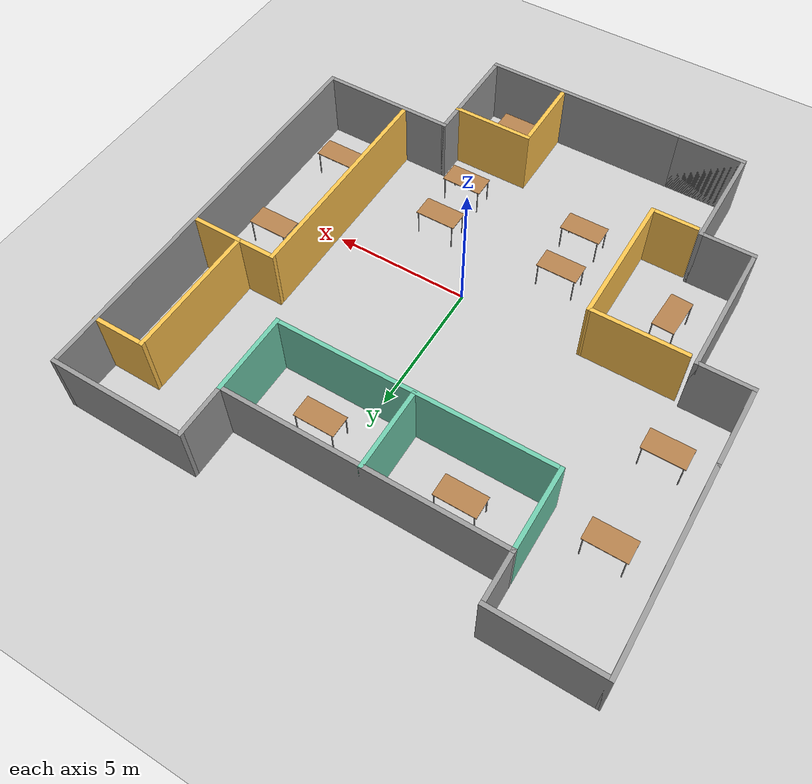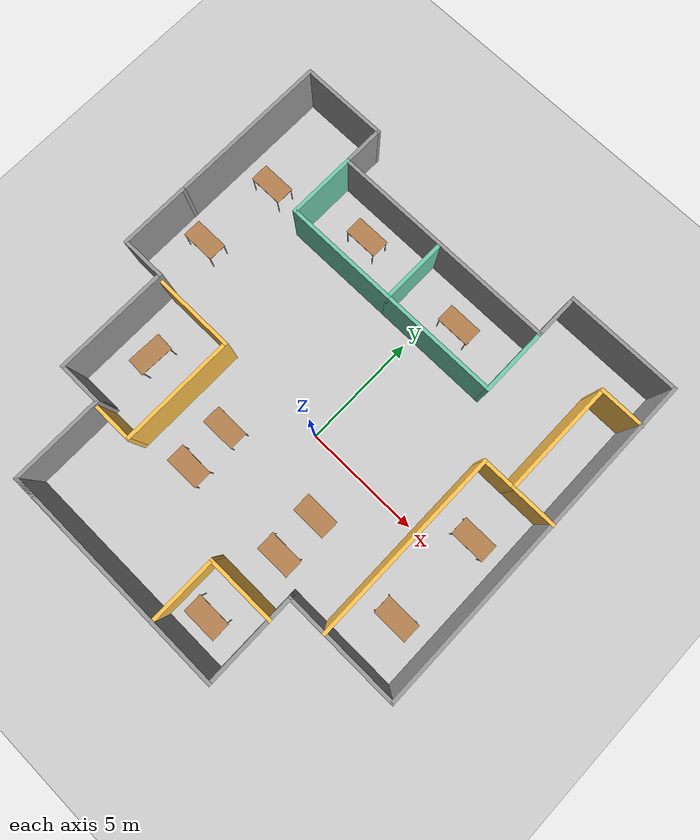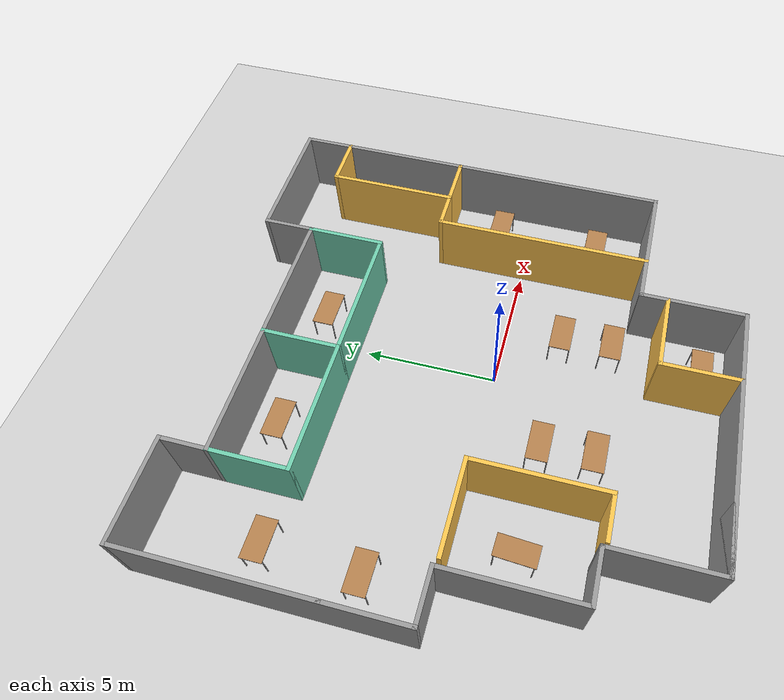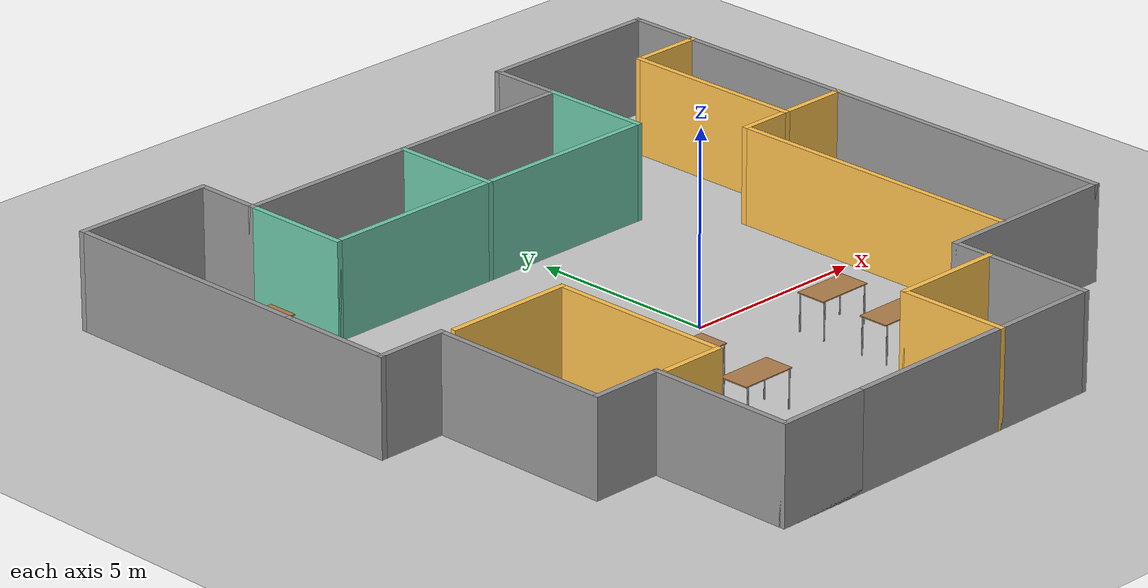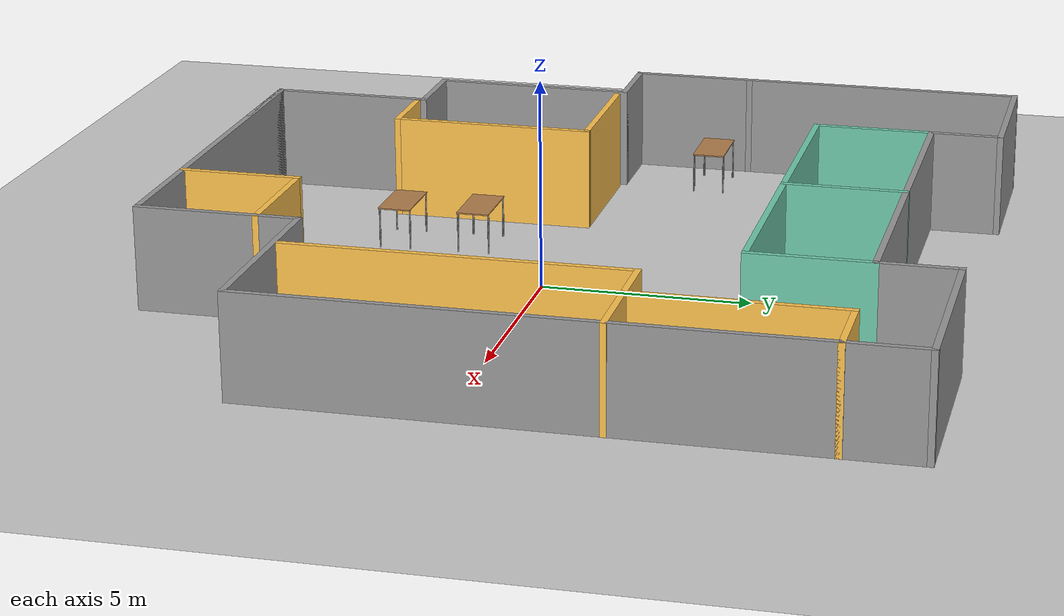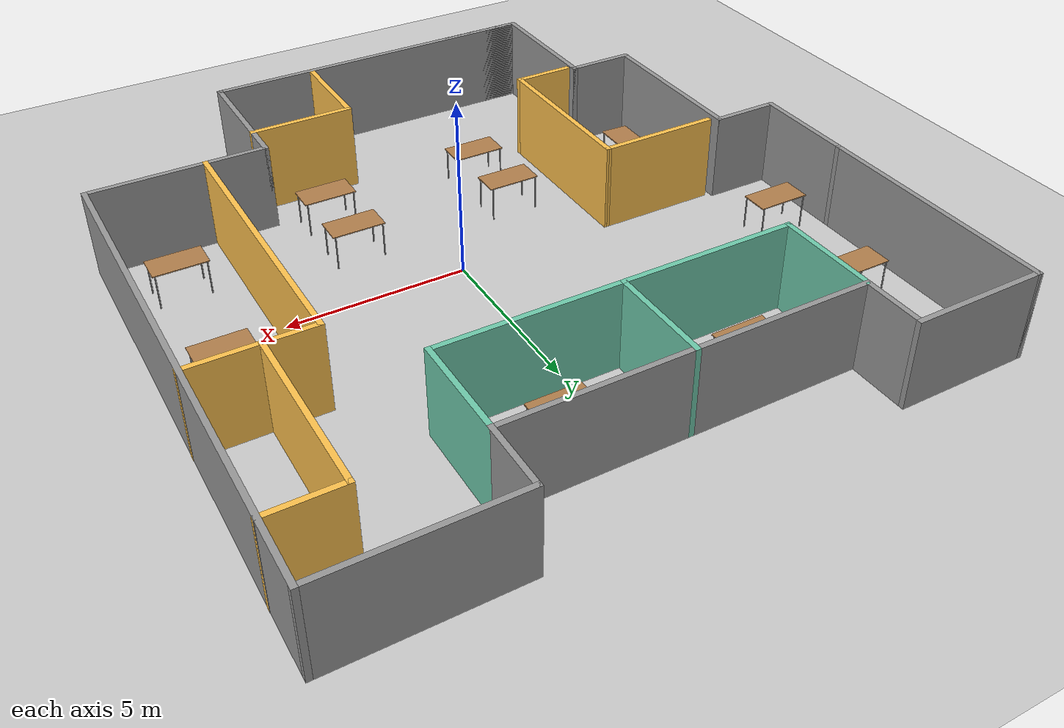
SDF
<sdf version="1.6">
 <world name="default">
  <plugin name="hello" filename="libhello.so"/>
  <light name="sun" type="directional">
   <pose>0 0 10 0 -0 0</pose>
   <diffuse>0.8 0.8 0.8 1</diffuse>
   <specular>0.2 0.2 0.2 1</specular>
   <attenuation>
    <range>1000</range>
    <constant>0.9</constant>
    <linear>0.01</linear>
    <quadratic>0.001</quadratic>
   </attenuation>
   <direction>-0.5 0.1 -0.9</direction>
  </light>
  <model name="ground_plane">
   <static>1</static>
   <link name="link">
    <collision name="collision">
     <geometry><plane><normal>0 0 1</normal><size>100 100</size></plane></geometry>
     <surface>
      <contact><collide_bitmask>65535</collide_bitmask></contact>
      <friction><ode><mu>100</mu><mu2>50</mu2></ode></friction>
     </surface>
    </collision>
    <visual name="visual">
     <cast_shadows>0</cast_shadows>
     <geometry><plane><normal>0 0 1</normal><size>100 100</size></plane></geometry>
     <material>
      <script><uri>file://media/materials/scripts/gazebo.material</uri><name>Gazebo/Grey</name></script>
     </material>
    </visual>
   </link>
  </model>
  <gravity>0 0 -9.8</gravity>
  <magnetic_field>6e-06 2.3e-05 -4.2e-05</magnetic_field>
  <atmosphere type="adiabatic"/>
  <physics name="default_physics" default="0" type="ode">
   <max_step_size>0.001</max_step_size>
   <real_time_factor>1</real_time_factor>
   <real_time_update_rate>1000</real_time_update_rate>
  </physics>
  <scene><ambient>0.4 0.4 0.4 1</ambient><background>0.7 0.7 0.7 1</background><shadows>1</shadows></scene>
  <audio><device>default</device></audio>
  <spherical_coordinates>
   <surface_model>EARTH_WGS84</surface_model>
   <latitude_deg>0</latitude_deg>
   <longitude_deg>0</longitude_deg>
   <elevation>0</elevation>
   <heading_deg>0</heading_deg>
  </spherical_coordinates>
  <model name="model">
   <link name="Wall_0">
    <pose>-9.205 4.275 0 0 0 -1.5708</pose>
    <visual name="Wall_0_Visual">
     <pose>0 0 1.25 0 -0 0</pose>
     <geometry><box><size>10 0.15 2.5</size></box></geometry>
     <material>
      <script><uri>file://media/materials/scripts/gazebo.material</uri><name>Gazebo/Grey</name></script>
      <ambient>1 1 1 1</ambient>
     </material>
     <meta><layer>0</layer></meta>
    </visual>
    <collision name="Wall_0_Collision">
     <pose>0 0 1.25 0 -0 0</pose>
     <geometry><box><size>10 0.15 2.5</size></box></geometry>
     <surface>
      <friction>
       <ode><mu>1</mu><mu2>1</mu2><fdir1>0 0 0</fdir1><slip1>0</slip1><slip2>0</slip2></ode>
       <torsional>
        <coefficient>1</coefficient>
        <patch_radius>0</patch_radius>
        <surface_radius>0</surface_radius>
        <use_patch_radius>1</use_patch_radius>
        <ode><slip>0</slip></ode>
       </torsional>
      </friction>
      <bounce><restitution_coefficient>0</restitution_coefficient><threshold>1e+06</threshold></bounce>
      <contact>
       <collide_without_contact>0</collide_without_contact>
       <collide_without_contact_bitmask>1</collide_without_contact_bitmask>
       <collide_bitmask>1</collide_bitmask>
       <ode>
        <soft_cfm>0</soft_cfm>
        <soft_erp>0.2</soft_erp>
        <kp>1e+13</kp>
        <kd>1</kd>
        <max_vel>0.01</max_vel>
        <min_depth>0</min_depth>
       </ode>
       <bullet>
        <split_impulse>1</split_impulse>
        <split_impulse_penetration_threshold>-0.01</split_impulse_penetration_threshold>
        <soft_cfm>0</soft_cfm>
        <soft_erp>0.2</soft_erp>
        <kp>1e+13</kp>
        <kd>1</kd>
       </bullet>
      </contact>
     </surface>
    </collision>
   </link>
   <link name="Wall_10">
    <pose>6.77 -5.5 0 0 -0 0</pose>
    <visual name="Wall_10_Visual">
     <pose>0 0 1.25 0 -0 0</pose>
     <geometry><box><size>5 0.15 2.5</size></box></geometry>
     <material>
      <script><uri>file://media/materials/scripts/gazebo.material</uri><name>Gazebo/Grey</name></script>
      <ambient>1 1 1 1</ambient>
     </material>
     <meta><layer>0</layer></meta>
    </visual>
    <collision name="Wall_10_Collision">
     <pose>0 0 1.25 0 -0 0</pose>
     <geometry><box><size>5 0.15 2.5</size></box></geometry>
     <surface>
      <friction>
       <ode><mu>1</mu><mu2>1</mu2><fdir1>0 0 0</fdir1><slip1>0</slip1><slip2>0</slip2></ode>
       <torsional>
        <coefficient>1</coefficient>
        <patch_radius>0</patch_radius>
        <surface_radius>0</surface_radius>
        <use_patch_radius>1</use_patch_radius>
        <ode><slip>0</slip></ode>
       </torsional>
      </friction>
      <bounce><restitution_coefficient>0</restitution_coefficient><threshold>1e+06</threshold></bounce>
      <contact>
       <collide_without_contact>0</collide_without_contact>
       <collide_without_contact_bitmask>1</collide_without_contact_bitmask>
       <collide_bitmask>1</collide_bitmask>
       <ode>
        <soft_cfm>0</soft_cfm>
        <soft_erp>0.2</soft_erp>
        <kp>1e+13</kp>
        <kd>1</kd>
        <max_vel>0.01</max_vel>
        <min_depth>0</min_depth>
       </ode>
       <bullet>
        <split_impulse>1</split_impulse>
        <split_impulse_penetration_threshold>-0.01</split_impulse_penetration_threshold>
        <soft_cfm>0</soft_cfm>
        <soft_erp>0.2</soft_erp>
        <kp>1e+13</kp>
        <kd>1</kd>
       </bullet>
      </contact>
     </surface>
    </collision>
   </link>
   <link name="Wall_12">
    <pose>9.195 1.925 0 0 -0 1.5708</pose>
    <visual name="Wall_12_Visual">
     <pose>0 0 1.25 0 -0 0</pose>
     <geometry><box><size>15 0.15 2.5</size></box></geometry>
     <material>
      <script><uri>file://media/materials/scripts/gazebo.material</uri><name>Gazebo/Grey</name></script>
      <ambient>1 1 1 1</ambient>
     </material>
     <meta><layer>0</layer></meta>
    </visual>
    <collision name="Wall_12_Collision">
     <pose>0 0 1.25 0 -0 0</pose>
     <geometry><box><size>15 0.15 2.5</size></box></geometry>
     <surface>
      <friction>
       <ode><mu>1</mu><mu2>1</mu2><fdir1>0 0 0</fdir1><slip1>0</slip1><slip2>0</slip2></ode>
       <torsional>
        <coefficient>1</coefficient>
        <patch_radius>0</patch_radius>
        <surface_radius>0</surface_radius>
        <use_patch_radius>1</use_patch_radius>
        <ode><slip>0</slip></ode>
       </torsional>
      </friction>
      <bounce><restitution_coefficient>0</restitution_coefficient><threshold>1e+06</threshold></bounce>
      <contact>
       <collide_without_contact>0</collide_without_contact>
       <collide_without_contact_bitmask>1</collide_without_contact_bitmask>
       <collide_bitmask>1</collide_bitmask>
       <ode>
        <soft_cfm>0</soft_cfm>
        <soft_erp>0.2</soft_erp>
        <kp>1e+13</kp>
        <kd>1</kd>
        <max_vel>0.01</max_vel>
        <min_depth>0</min_depth>
       </ode>
       <bullet>
        <split_impulse>1</split_impulse>
        <split_impulse_penetration_threshold>-0.01</split_impulse_penetration_threshold>
        <soft_cfm>0</soft_cfm>
        <soft_erp>0.2</soft_erp>
        <kp>1e+13</kp>
        <kd>1</kd>
       </bullet>
      </contact>
     </surface>
    </collision>
   </link>
   <link name="Wall_13">
    <pose>6.77 9.35 0 0 -0 3.14159</pose>
    <visual name="Wall_13_Visual">
     <pose>0 0 1.25 0 -0 0</pose>
     <geometry><box><size>5 0.15 2.5</size></box></geometry>
     <material>
      <script><uri>file://media/materials/scripts/gazebo.material</uri><name>Gazebo/Grey</name></script>
      <ambient>1 1 1 1</ambient>
     </material>
     <meta><layer>0</layer></meta>
    </visual>
    <collision name="Wall_13_Collision">
     <pose>0 0 1.25 0 -0 0</pose>
     <geometry><box><size>5 0.15 2.5</size></box></geometry>
     <surface>
      <friction>
       <ode><mu>1</mu><mu2>1</mu2><fdir1>0 0 0</fdir1><slip1>0</slip1><slip2>0</slip2></ode>
       <torsional>
        <coefficient>1</coefficient>
        <patch_radius>0</patch_radius>
        <surface_radius>0</surface_radius>
        <use_patch_radius>1</use_patch_radius>
        <ode><slip>0</slip></ode>
       </torsional>
      </friction>
      <bounce><restitution_coefficient>0</restitution_coefficient><threshold>1e+06</threshold></bounce>
      <contact>
       <collide_without_contact>0</collide_without_contact>
       <collide_without_contact_bitmask>1</collide_without_contact_bitmask>
       <collide_bitmask>1</collide_bitmask>
       <ode>
        <soft_cfm>0</soft_cfm>
        <soft_erp>0.2</soft_erp>
        <kp>1e+13</kp>
        <kd>1</kd>
        <max_vel>0.01</max_vel>
        <min_depth>0</min_depth>
       </ode>
       <bullet>
        <split_impulse>1</split_impulse>
        <split_impulse_penetration_threshold>-0.01</split_impulse_penetration_threshold>
        <soft_cfm>0</soft_cfm>
        <soft_erp>0.2</soft_erp>
        <kp>1e+13</kp>
        <kd>1</kd>
       </bullet>
      </contact>
     </surface>
    </collision>
   </link>
   <link name="Wall_14">
    <pose>4.345 8.425 0 0 0 -1.5708</pose>
    <visual name="Wall_14_Visual">
     <pose>0 0 1.25 0 -0 0</pose>
     <geometry><box><size>2 0.15 2.5</size></box></geometry>
     <material>
      <script><uri>file://media/materials/scripts/gazebo.material</uri><name>Gazebo/Grey</name></script>
      <ambient>1 1 1 1</ambient>
     </material>
     <meta><layer>0</layer></meta>
    </visual>
    <collision name="Wall_14_Collision">
     <pose>0 0 1.25 0 -0 0</pose>
     <geometry><box><size>2 0.15 2.5</size></box></geometry>
     <surface>
      <friction>
       <ode><mu>1</mu><mu2>1</mu2><fdir1>0 0 0</fdir1><slip1>0</slip1><slip2>0</slip2></ode>
       <torsional>
        <coefficient>1</coefficient>
        <patch_radius>0</patch_radius>
        <surface_radius>0</surface_radius>
        <use_patch_radius>1</use_patch_radius>
        <ode><slip>0</slip></ode>
       </torsional>
      </friction>
      <bounce><restitution_coefficient>0</restitution_coefficient><threshold>1e+06</threshold></bounce>
      <contact>
       <collide_without_contact>0</collide_without_contact>
       <collide_without_contact_bitmask>1</collide_without_contact_bitmask>
       <collide_bitmask>1</collide_bitmask>
       <ode>
        <soft_cfm>0</soft_cfm>
        <soft_erp>0.2</soft_erp>
        <kp>1e+13</kp>
        <kd>1</kd>
        <max_vel>0.01</max_vel>
        <min_depth>0</min_depth>
       </ode>
       <bullet>
        <split_impulse>1</split_impulse>
        <split_impulse_penetration_threshold>-0.01</split_impulse_penetration_threshold>
        <soft_cfm>0</soft_cfm>
        <soft_erp>0.2</soft_erp>
        <kp>1e+13</kp>
        <kd>1</kd>
       </bullet>
      </contact>
     </surface>
    </collision>
   </link>
   <link name="Wall_15">
    <pose>-0.58 7.5 0 0 -0 3.14159</pose>
    <visual name="Wall_15_Visual">
     <pose>0 0 1.25 0 -0 0</pose>
     <geometry><box><size>10 0.15 2.5</size></box></geometry>
     <material>
      <script><uri>file://media/materials/scripts/gazebo.material</uri><name>Gazebo/Grey</name></script>
      <ambient>1 1 1 1</ambient>
     </material>
     <meta><layer>0</layer></meta>
    </visual>
    <collision name="Wall_15_Collision">
     <pose>0 0 1.25 0 -0 0</pose>
     <geometry><box><size>10 0.15 2.5</size></box></geometry>
     <surface>
      <friction>
       <ode><mu>1</mu><mu2>1</mu2><fdir1>0 0 0</fdir1><slip1>0</slip1><slip2>0</slip2></ode>
       <torsional>
        <coefficient>1</coefficient>
        <patch_radius>0</patch_radius>
        <surface_radius>0</surface_radius>
        <use_patch_radius>1</use_patch_radius>
        <ode><slip>0</slip></ode>
       </torsional>
      </friction>
      <bounce><restitution_coefficient>0</restitution_coefficient><threshold>1e+06</threshold></bounce>
      <contact>
       <collide_without_contact>0</collide_without_contact>
       <collide_without_contact_bitmask>1</collide_without_contact_bitmask>
       <collide_bitmask>1</collide_bitmask>
       <ode>
        <soft_cfm>0</soft_cfm>
        <soft_erp>0.2</soft_erp>
        <kp>1e+13</kp>
        <kd>1</kd>
        <max_vel>0.01</max_vel>
        <min_depth>0</min_depth>
       </ode>
       <bullet>
        <split_impulse>1</split_impulse>
        <split_impulse_penetration_threshold>-0.01</split_impulse_penetration_threshold>
        <soft_cfm>0</soft_cfm>
        <soft_erp>0.2</soft_erp>
        <kp>1e+13</kp>
        <kd>1</kd>
       </bullet>
      </contact>
     </surface>
    </collision>
   </link>
   <link name="Wall_16">
    <pose>-5.505 8.3 0 0 -0 1.5708</pose>
    <visual name="Wall_16_Visual">
     <pose>0 0 1.25 0 -0 0</pose>
     <geometry><box><size>1.75 0.15 2.5</size></box></geometry>
     <material>
      <script><uri>file://media/materials/scripts/gazebo.material</uri><name>Gazebo/Grey</name></script>
      <ambient>1 1 1 1</ambient>
     </material>
     <meta><layer>0</layer></meta>
    </visual>
    <collision name="Wall_16_Collision">
     <pose>0 0 1.25 0 -0 0</pose>
     <geometry><box><size>1.75 0.15 2.5</size></box></geometry>
     <surface>
      <friction>
       <ode><mu>1</mu><mu2>1</mu2><fdir1>0 0 0</fdir1><slip1>0</slip1><slip2>0</slip2></ode>
       <torsional>
        <coefficient>1</coefficient>
        <patch_radius>0</patch_radius>
        <surface_radius>0</surface_radius>
        <use_patch_radius>1</use_patch_radius>
        <ode><slip>0</slip></ode>
       </torsional>
      </friction>
      <bounce><restitution_coefficient>0</restitution_coefficient><threshold>1e+06</threshold></bounce>
      <contact>
       <collide_without_contact>0</collide_without_contact>
       <collide_without_contact_bitmask>1</collide_without_contact_bitmask>
       <collide_bitmask>1</collide_bitmask>
       <ode>
        <soft_cfm>0</soft_cfm>
        <soft_erp>0.2</soft_erp>
        <kp>1e+13</kp>
        <kd>1</kd>
        <max_vel>0.01</max_vel>
        <min_depth>0</min_depth>
       </ode>
       <bullet>
        <split_impulse>1</split_impulse>
        <split_impulse_penetration_threshold>-0.01</split_impulse_penetration_threshold>
        <soft_cfm>0</soft_cfm>
        <soft_erp>0.2</soft_erp>
        <kp>1e+13</kp>
        <kd>1</kd>
       </bullet>
      </contact>
     </surface>
    </collision>
   </link>
   <link name="Wall_18">
    <pose>-5.505 6.075 0 0 0 -1.5708</pose>
    <visual name="Wall_18_Visual">
     <pose>0 0 1.25 0 -0 0</pose>
     <geometry><box><size>3 0.15 2.5</size></box></geometry>
     <material>
      <script><uri>file://media/materials/scripts/gazebo.material</uri><name>Gazebo/Grey</name></script>
      <ambient>0.435294 0.796078 0.67451 1</ambient>
     </material>
     <meta><layer>0</layer></meta>
    </visual>
    <collision name="Wall_18_Collision">
     <pose>0 0 1.25 0 -0 0</pose>
     <geometry><box><size>3 0.15 2.5</size></box></geometry>
     <surface>
      <friction>
       <ode><mu>1</mu><mu2>1</mu2><fdir1>0 0 0</fdir1><slip1>0</slip1><slip2>0</slip2></ode>
       <torsional>
        <coefficient>1</coefficient>
        <patch_radius>0</patch_radius>
        <surface_radius>0</surface_radius>
        <use_patch_radius>1</use_patch_radius>
        <ode><slip>0</slip></ode>
       </torsional>
      </friction>
      <bounce><restitution_coefficient>0</restitution_coefficient><threshold>1e+06</threshold></bounce>
      <contact>
       <collide_without_contact>0</collide_without_contact>
       <collide_without_contact_bitmask>1</collide_without_contact_bitmask>
       <collide_bitmask>1</collide_bitmask>
       <ode>
        <soft_cfm>0</soft_cfm>
        <soft_erp>0.2</soft_erp>
        <kp>1e+13</kp>
        <kd>1</kd>
        <max_vel>0.01</max_vel>
        <min_depth>0</min_depth>
       </ode>
       <bullet>
        <split_impulse>1</split_impulse>
        <split_impulse_penetration_threshold>-0.01</split_impulse_penetration_threshold>
        <soft_cfm>0</soft_cfm>
        <soft_erp>0.2</soft_erp>
        <kp>1e+13</kp>
        <kd>1</kd>
       </bullet>
      </contact>
     </surface>
    </collision>
   </link>
   <link name="Wall_19">
    <pose>-3.08 4.65 0 0 -0 0</pose>
    <visual name="Wall_19_Visual">
     <pose>0 0 1.25 0 -0 0</pose>
     <geometry><box><size>5 0.15 2.5</size></box></geometry>
     <material>
      <script><uri>file://media/materials/scripts/gazebo.material</uri><name>Gazebo/Grey</name></script>
      <ambient>0.435294 0.796078 0.67451 1</ambient>
     </material>
     <meta><layer>0</layer></meta>
    </visual>
    <collision name="Wall_19_Collision">
     <pose>0 0 1.25 0 -0 0</pose>
     <geometry><box><size>5 0.15 2.5</size></box></geometry>
     <surface>
      <friction>
       <ode><mu>1</mu><mu2>1</mu2><fdir1>0 0 0</fdir1><slip1>0</slip1><slip2>0</slip2></ode>
       <torsional>
        <coefficient>1</coefficient>
        <patch_radius>0</patch_radius>
        <surface_radius>0</surface_radius>
        <use_patch_radius>1</use_patch_radius>
        <ode><slip>0</slip></ode>
       </torsional>
      </friction>
      <bounce><restitution_coefficient>0</restitution_coefficient><threshold>1e+06</threshold></bounce>
      <contact>
       <collide_without_contact>0</collide_without_contact>
       <collide_without_contact_bitmask>1</collide_without_contact_bitmask>
       <collide_bitmask>1</collide_bitmask>
       <ode>
        <soft_cfm>0</soft_cfm>
        <soft_erp>0.2</soft_erp>
        <kp>1e+13</kp>
        <kd>1</kd>
        <max_vel>0.01</max_vel>
        <min_depth>0</min_depth>
       </ode>
       <bullet>
        <split_impulse>1</split_impulse>
        <split_impulse_penetration_threshold>-0.01</split_impulse_penetration_threshold>
        <soft_cfm>0</soft_cfm>
        <soft_erp>0.2</soft_erp>
        <kp>1e+13</kp>
        <kd>1</kd>
       </bullet>
      </contact>
     </surface>
    </collision>
   </link>
   <link name="Wall_2">
    <pose>-7.355 9.2 0 0 -0 0</pose>
    <visual name="Wall_2_Visual">
     <pose>0 0 1.25 0 -0 0</pose>
     <geometry><box><size>3.85 0.15 2.5</size></box></geometry>
     <material>
      <script><uri>file://media/materials/scripts/gazebo.material</uri><name>Gazebo/Grey</name></script>
      <ambient>1 1 1 1</ambient>
     </material>
     <meta><layer>0</layer></meta>
    </visual>
    <collision name="Wall_2_Collision">
     <pose>0 0 1.25 0 -0 0</pose>
     <geometry><box><size>3.85 0.15 2.5</size></box></geometry>
     <surface>
      <friction>
       <ode><mu>1</mu><mu2>1</mu2><fdir1>0 0 0</fdir1><slip1>0</slip1><slip2>0</slip2></ode>
       <torsional>
        <coefficient>1</coefficient>
        <patch_radius>0</patch_radius>
        <surface_radius>0</surface_radius>
        <use_patch_radius>1</use_patch_radius>
        <ode><slip>0</slip></ode>
       </torsional>
      </friction>
      <bounce><restitution_coefficient>0</restitution_coefficient><threshold>1e+06</threshold></bounce>
      <contact>
       <collide_without_contact>0</collide_without_contact>
       <collide_without_contact_bitmask>1</collide_without_contact_bitmask>
       <collide_bitmask>1</collide_bitmask>
       <ode>
        <soft_cfm>0</soft_cfm>
        <soft_erp>0.2</soft_erp>
        <kp>1e+13</kp>
        <kd>1</kd>
        <max_vel>0.01</max_vel>
        <min_depth>0</min_depth>
       </ode>
       <bullet>
        <split_impulse>1</split_impulse>
        <split_impulse_penetration_threshold>-0.01</split_impulse_penetration_threshold>
        <soft_cfm>0</soft_cfm>
        <soft_erp>0.2</soft_erp>
        <kp>1e+13</kp>
        <kd>1</kd>
       </bullet>
      </contact>
     </surface>
    </collision>
   </link>
   <link name="Wall_20">
    <pose>-0.655 6.075 0 0 -0 1.5708</pose>
    <visual name="Wall_20_Visual">
     <pose>0 0 1.25 0 -0 0</pose>
     <geometry><box><size>3 0.15 2.5</size></box></geometry>
     <material>
      <script><uri>file://media/materials/scripts/gazebo.material</uri><name>Gazebo/Grey</name></script>
      <ambient>0.435294 0.796078 0.67451 1</ambient>
     </material>
     <meta><layer>0</layer></meta>
    </visual>
    <collision name="Wall_20_Collision">
     <pose>0 0 1.25 0 -0 0</pose>
     <geometry><box><size>3 0.15 2.5</size></box></geometry>
     <surface>
      <friction>
       <ode><mu>1</mu><mu2>1</mu2><fdir1>0 0 0</fdir1><slip1>0</slip1><slip2>0</slip2></ode>
       <torsional>
        <coefficient>1</coefficient>
        <patch_radius>0</patch_radius>
        <surface_radius>0</surface_radius>
        <use_patch_radius>1</use_patch_radius>
        <ode><slip>0</slip></ode>
       </torsional>
      </friction>
      <bounce><restitution_coefficient>0</restitution_coefficient><threshold>1e+06</threshold></bounce>
      <contact>
       <collide_without_contact>0</collide_without_contact>
       <collide_without_contact_bitmask>1</collide_without_contact_bitmask>
       <collide_bitmask>1</collide_bitmask>
       <ode>
        <soft_cfm>0</soft_cfm>
        <soft_erp>0.2</soft_erp>
        <kp>1e+13</kp>
        <kd>1</kd>
        <max_vel>0.01</max_vel>
        <min_depth>0</min_depth>
       </ode>
       <bullet>
        <split_impulse>1</split_impulse>
        <split_impulse_penetration_threshold>-0.01</split_impulse_penetration_threshold>
        <soft_cfm>0</soft_cfm>
        <soft_erp>0.2</soft_erp>
        <kp>1e+13</kp>
        <kd>1</kd>
       </bullet>
      </contact>
     </surface>
    </collision>
   </link>
   <link name="Wall_21">
    <pose>1.77 4.65 0 0 -0 0</pose>
    <visual name="Wall_21_Visual">
     <pose>0 0 1.25 0 -0 0</pose>
     <geometry><box><size>5 0.15 2.5</size></box></geometry>
     <material>
      <script><uri>file://media/materials/scripts/gazebo.material</uri><name>Gazebo/Grey</name></script>
      <ambient>0.435294 0.796078 0.67451 1</ambient>
     </material>
     <meta><layer>0</layer></meta>
    </visual>
    <collision name="Wall_21_Collision">
     <pose>0 0 1.25 0 -0 0</pose>
     <geometry><box><size>5 0.15 2.5</size></box></geometry>
     <surface>
      <friction>
       <ode><mu>1</mu><mu2>1</mu2><fdir1>0 0 0</fdir1><slip1>0</slip1><slip2>0</slip2></ode>
       <torsional>
        <coefficient>1</coefficient>
        <patch_radius>0</patch_radius>
        <surface_radius>0</surface_radius>
        <use_patch_radius>1</use_patch_radius>
        <ode><slip>0</slip></ode>
       </torsional>
      </friction>
      <bounce><restitution_coefficient>0</restitution_coefficient><threshold>1e+06</threshold></bounce>
      <contact>
       <collide_without_contact>0</collide_without_contact>
       <collide_without_contact_bitmask>1</collide_without_contact_bitmask>
       <collide_bitmask>1</collide_bitmask>
       <ode>
        <soft_cfm>0</soft_cfm>
        <soft_erp>0.2</soft_erp>
        <kp>1e+13</kp>
        <kd>1</kd>
        <max_vel>0.01</max_vel>
        <min_depth>0</min_depth>
       </ode>
       <bullet>
        <split_impulse>1</split_impulse>
        <split_impulse_penetration_threshold>-0.01</split_impulse_penetration_threshold>
        <soft_cfm>0</soft_cfm>
        <soft_erp>0.2</soft_erp>
        <kp>1e+13</kp>
        <kd>1</kd>
       </bullet>
      </contact>
     </surface>
    </collision>
   </link>
   <link name="Wall_22">
    <pose>4.345 6.075 0 0 0 -1.5708</pose>
    <visual name="Wall_22_Visual">
     <pose>0 0 1.25 0 -0 0</pose>
     <geometry><box><size>3 0.15 2.5</size></box></geometry>
     <material>
      <script><uri>file://media/materials/scripts/gazebo.material</uri><name>Gazebo/Grey</name></script>
      <ambient>0.435294 0.796078 0.67451 1</ambient>
     </material>
     <meta><layer>0</layer></meta>
    </visual>
    <collision name="Wall_22_Collision">
     <pose>0 0 1.25 0 -0 0</pose>
     <geometry><box><size>3 0.15 2.5</size></box></geometry>
     <surface>
      <friction>
       <ode><mu>1</mu><mu2>1</mu2><fdir1>0 0 0</fdir1><slip1>0</slip1><slip2>0</slip2></ode>
       <torsional>
        <coefficient>1</coefficient>
        <patch_radius>0</patch_radius>
        <surface_radius>0</surface_radius>
        <use_patch_radius>1</use_patch_radius>
        <ode><slip>0</slip></ode>
       </torsional>
      </friction>
      <bounce><restitution_coefficient>0</restitution_coefficient><threshold>1e+06</threshold></bounce>
      <contact>
       <collide_without_contact>0</collide_without_contact>
       <collide_without_contact_bitmask>1</collide_without_contact_bitmask>
       <collide_bitmask>1</collide_bitmask>
       <ode>
        <soft_cfm>0</soft_cfm>
        <soft_erp>0.2</soft_erp>
        <kp>1e+13</kp>
        <kd>1</kd>
        <max_vel>0.01</max_vel>
        <min_depth>0</min_depth>
       </ode>
       <bullet>
        <split_impulse>1</split_impulse>
        <split_impulse_penetration_threshold>-0.01</split_impulse_penetration_threshold>
        <soft_cfm>0</soft_cfm>
        <soft_erp>0.2</soft_erp>
        <kp>1e+13</kp>
        <kd>1</kd>
       </bullet>
      </contact>
     </surface>
    </collision>
   </link>
   <link name="Wall_24">
    <pose>9.2 7.5 0 0 -0 0</pose>
    <visual name="Wall_24_Visual">
     <pose>0 0 1.25 0 -0 0</pose>
     <geometry><box><size>0.16 0.15 2.5</size></box></geometry>
     <material>
      <script><uri>file://media/materials/scripts/gazebo.material</uri><name>Gazebo/Grey</name></script>
      <ambient>1 1 1 1</ambient>
     </material>
     <meta><layer>0</layer></meta>
    </visual>
    <collision name="Wall_24_Collision">
     <pose>0 0 1.25 0 -0 0</pose>
     <geometry><box><size>0.16 0.15 2.5</size></box></geometry>
     <surface>
      <friction>
       <ode><mu>1</mu><mu2>1</mu2><fdir1>0 0 0</fdir1><slip1>0</slip1><slip2>0</slip2></ode>
       <torsional>
        <coefficient>1</coefficient>
        <patch_radius>0</patch_radius>
        <surface_radius>0</surface_radius>
        <use_patch_radius>1</use_patch_radius>
        <ode><slip>0</slip></ode>
       </torsional>
      </friction>
      <bounce><restitution_coefficient>0</restitution_coefficient><threshold>1e+06</threshold></bounce>
      <contact>
       <collide_without_contact>0</collide_without_contact>
       <collide_without_contact_bitmask>1</collide_without_contact_bitmask>
       <collide_bitmask>1</collide_bitmask>
       <ode>
        <soft_cfm>0</soft_cfm>
        <soft_erp>0.2</soft_erp>
        <kp>1e+13</kp>
        <kd>1</kd>
        <max_vel>0.01</max_vel>
        <min_depth>0</min_depth>
       </ode>
       <bullet>
        <split_impulse>1</split_impulse>
        <split_impulse_penetration_threshold>-0.01</split_impulse_penetration_threshold>
        <soft_cfm>0</soft_cfm>
        <soft_erp>0.2</soft_erp>
        <kp>1e+13</kp>
        <kd>1</kd>
       </bullet>
      </contact>
     </surface>
    </collision>
   </link>
   <link name="Wall_25">
    <pose>8.28 7.5 0 0 -0 3.14159</pose>
    <visual name="Wall_25_Visual">
     <pose>0 0 1.25 0 -0 0</pose>
     <geometry><box><size>2 0.15 2.5</size></box></geometry>
     <material>
      <script><uri>file://media/materials/scripts/gazebo.material</uri><name>Gazebo/Grey</name></script>
      <ambient>1 0.764706 0.305882 1</ambient>
     </material>
     <meta><layer>0</layer></meta>
    </visual>
    <collision name="Wall_25_Collision">
     <pose>0 0 1.25 0 -0 0</pose>
     <geometry><box><size>2 0.15 2.5</size></box></geometry>
     <surface>
      <friction>
       <ode><mu>1</mu><mu2>1</mu2><fdir1>0 0 0</fdir1><slip1>0</slip1><slip2>0</slip2></ode>
       <torsional>
        <coefficient>1</coefficient>
        <patch_radius>0</patch_radius>
        <surface_radius>0</surface_radius>
        <use_patch_radius>1</use_patch_radius>
        <ode><slip>0</slip></ode>
       </torsional>
      </friction>
      <bounce><restitution_coefficient>0</restitution_coefficient><threshold>1e+06</threshold></bounce>
      <contact>
       <collide_without_contact>0</collide_without_contact>
       <collide_without_contact_bitmask>1</collide_without_contact_bitmask>
       <collide_bitmask>1</collide_bitmask>
       <ode>
        <soft_cfm>0</soft_cfm>
        <soft_erp>0.2</soft_erp>
        <kp>1e+13</kp>
        <kd>1</kd>
        <max_vel>0.01</max_vel>
        <min_depth>0</min_depth>
       </ode>
       <bullet>
        <split_impulse>1</split_impulse>
        <split_impulse_penetration_threshold>-0.01</split_impulse_penetration_threshold>
        <soft_cfm>0</soft_cfm>
        <soft_erp>0.2</soft_erp>
        <kp>1e+13</kp>
        <kd>1</kd>
       </bullet>
      </contact>
     </surface>
    </collision>
   </link>
   <link name="Wall_26">
    <pose>7.355 5.075 0 0 0 -1.5708</pose>
    <visual name="Wall_26_Visual">
     <pose>0 0 1.25 0 -0 0</pose>
     <geometry><box><size>5 0.15 2.5</size></box></geometry>
     <material>
      <script><uri>file://media/materials/scripts/gazebo.material</uri><name>Gazebo/Grey</name></script>
      <ambient>1 0.764706 0.305882 1</ambient>
     </material>
     <meta><layer>0</layer></meta>
    </visual>
    <collision name="Wall_26_Collision">
     <pose>0 0 1.25 0 -0 0</pose>
     <geometry><box><size>5 0.15 2.5</size></box></geometry>
     <surface>
      <friction>
       <ode><mu>1</mu><mu2>1</mu2><fdir1>0 0 0</fdir1><slip1>0</slip1><slip2>0</slip2></ode>
       <torsional>
        <coefficient>1</coefficient>
        <patch_radius>0</patch_radius>
        <surface_radius>0</surface_radius>
        <use_patch_radius>1</use_patch_radius>
        <ode><slip>0</slip></ode>
       </torsional>
      </friction>
      <bounce><restitution_coefficient>0</restitution_coefficient><threshold>1e+06</threshold></bounce>
      <contact>
       <collide_without_contact>0</collide_without_contact>
       <collide_without_contact_bitmask>1</collide_without_contact_bitmask>
       <collide_bitmask>1</collide_bitmask>
       <ode>
        <soft_cfm>0</soft_cfm>
        <soft_erp>0.2</soft_erp>
        <kp>1e+13</kp>
        <kd>1</kd>
        <max_vel>0.01</max_vel>
        <min_depth>0</min_depth>
       </ode>
       <bullet>
        <split_impulse>1</split_impulse>
        <split_impulse_penetration_threshold>-0.01</split_impulse_penetration_threshold>
        <soft_cfm>0</soft_cfm>
        <soft_erp>0.2</soft_erp>
        <kp>1e+13</kp>
        <kd>1</kd>
       </bullet>
      </contact>
     </surface>
    </collision>
   </link>
   <link name="Wall_29">
    <pose>8.28 2.65 0 0 -0 0</pose>
    <visual name="Wall_29_Visual">
     <pose>0 0 1.25 0 -0 0</pose>
     <geometry><box><size>2 0.15 2.5</size></box></geometry>
     <material>
      <script><uri>file://media/materials/scripts/gazebo.material</uri><name>Gazebo/Grey</name></script>
      <ambient>1 0.764706 0.305882 1</ambient>
     </material>
     <meta><layer>0</layer></meta>
    </visual>
    <collision name="Wall_29_Collision">
     <pose>0 0 1.25 0 -0 0</pose>
     <geometry><box><size>2 0.15 2.5</size></box></geometry>
     <surface>
      <friction>
       <ode><mu>1</mu><mu2>1</mu2><fdir1>0 0 0</fdir1><slip1>0</slip1><slip2>0</slip2></ode>
       <torsional>
        <coefficient>1</coefficient>
        <patch_radius>0</patch_radius>
        <surface_radius>0</surface_radius>
        <use_patch_radius>1</use_patch_radius>
        <ode><slip>0</slip></ode>
       </torsional>
      </friction>
      <bounce><restitution_coefficient>0</restitution_coefficient><threshold>1e+06</threshold></bounce>
      <contact>
       <collide_without_contact>0</collide_without_contact>
       <collide_without_contact_bitmask>1</collide_without_contact_bitmask>
       <collide_bitmask>1</collide_bitmask>
       <ode>
        <soft_cfm>0</soft_cfm>
        <soft_erp>0.2</soft_erp>
        <kp>1e+13</kp>
        <kd>1</kd>
        <max_vel>0.01</max_vel>
        <min_depth>0</min_depth>
       </ode>
       <bullet>
        <split_impulse>1</split_impulse>
        <split_impulse_penetration_threshold>-0.01</split_impulse_penetration_threshold>
        <soft_cfm>0</soft_cfm>
        <soft_erp>0.2</soft_erp>
        <kp>1e+13</kp>
        <kd>1</kd>
       </bullet>
      </contact>
     </surface>
    </collision>
   </link>
   <link name="Wall_3">
    <pose>-8.28 -0.65 0 0 -0 0</pose>
    <visual name="Wall_3_Visual">
     <pose>0 0 1.25 0 -0 0</pose>
     <geometry><box><size>2 0.15 2.5</size></box></geometry>
     <material>
      <script><uri>file://media/materials/scripts/gazebo.material</uri><name>Gazebo/Grey</name></script>
      <ambient>1 1 1 1</ambient>
     </material>
     <meta><layer>0</layer></meta>
    </visual>
    <collision name="Wall_3_Collision">
     <pose>0 0 1.25 0 -0 0</pose>
     <geometry><box><size>2 0.15 2.5</size></box></geometry>
     <surface>
      <friction>
       <ode><mu>1</mu><mu2>1</mu2><fdir1>0 0 0</fdir1><slip1>0</slip1><slip2>0</slip2></ode>
       <torsional>
        <coefficient>1</coefficient>
        <patch_radius>0</patch_radius>
        <surface_radius>0</surface_radius>
        <use_patch_radius>1</use_patch_radius>
        <ode><slip>0</slip></ode>
       </torsional>
      </friction>
      <bounce><restitution_coefficient>0</restitution_coefficient><threshold>1e+06</threshold></bounce>
      <contact>
       <collide_without_contact>0</collide_without_contact>
       <collide_without_contact_bitmask>1</collide_without_contact_bitmask>
       <collide_bitmask>1</collide_bitmask>
       <ode>
        <soft_cfm>0</soft_cfm>
        <soft_erp>0.2</soft_erp>
        <kp>1e+13</kp>
        <kd>1</kd>
        <max_vel>0.01</max_vel>
        <min_depth>0</min_depth>
       </ode>
       <bullet>
        <split_impulse>1</split_impulse>
        <split_impulse_penetration_threshold>-0.01</split_impulse_penetration_threshold>
        <soft_cfm>0</soft_cfm>
        <soft_erp>0.2</soft_erp>
        <kp>1e+13</kp>
        <kd>1</kd>
       </bullet>
      </contact>
     </surface>
    </collision>
   </link>
   <link name="Wall_31">
    <pose>6.68 2.65 0 0 -0 3.14159</pose>
    <visual name="Wall_31_Visual">
     <pose>0 0 1.25 0 -0 0</pose>
     <geometry><box><size>1.5 0.15 2.5</size></box></geometry>
     <material>
      <script><uri>file://media/materials/scripts/gazebo.material</uri><name>Gazebo/Grey</name></script>
      <ambient>1 0.764706 0.305882 1</ambient>
     </material>
     <meta><layer>0</layer></meta>
    </visual>
    <collision name="Wall_31_Collision">
     <pose>0 0 1.25 0 -0 0</pose>
     <geometry><box><size>1.5 0.15 2.5</size></box></geometry>
     <surface>
      <friction>
       <ode><mu>1</mu><mu2>1</mu2><fdir1>0 0 0</fdir1><slip1>0</slip1><slip2>0</slip2></ode>
       <torsional>
        <coefficient>1</coefficient>
        <patch_radius>0</patch_radius>
        <surface_radius>0</surface_radius>
        <use_patch_radius>1</use_patch_radius>
        <ode><slip>0</slip></ode>
       </torsional>
      </friction>
      <bounce><restitution_coefficient>0</restitution_coefficient><threshold>1e+06</threshold></bounce>
      <contact>
       <collide_without_contact>0</collide_without_contact>
       <collide_without_contact_bitmask>1</collide_without_contact_bitmask>
       <collide_bitmask>1</collide_bitmask>
       <ode>
        <soft_cfm>0</soft_cfm>
        <soft_erp>0.2</soft_erp>
        <kp>1e+13</kp>
        <kd>1</kd>
        <max_vel>0.01</max_vel>
        <min_depth>0</min_depth>
       </ode>
       <bullet>
        <split_impulse>1</split_impulse>
        <split_impulse_penetration_threshold>-0.01</split_impulse_penetration_threshold>
        <soft_cfm>0</soft_cfm>
        <soft_erp>0.2</soft_erp>
        <kp>1e+13</kp>
        <kd>1</kd>
       </bullet>
      </contact>
     </surface>
    </collision>
   </link>
   <link name="Wall_32">
    <pose>6.005 -1.425 0 0 0 -1.5708</pose>
    <visual name="Wall_32_Visual">
     <pose>0 0 1.25 0 -0 0</pose>
     <geometry><box><size>8.3 0.15 2.5</size></box></geometry>
     <material>
      <script><uri>file://media/materials/scripts/gazebo.material</uri><name>Gazebo/Grey</name></script>
      <ambient>1 0.764706 0.305882 1</ambient>
     </material>
     <meta><layer>0</layer></meta>
    </visual>
    <collision name="Wall_32_Collision">
     <pose>0 0 1.25 0 -0 0</pose>
     <geometry><box><size>8.3 0.15 2.5</size></box></geometry>
     <surface>
      <friction>
       <ode><mu>1</mu><mu2>1</mu2><fdir1>0 0 0</fdir1><slip1>0</slip1><slip2>0</slip2></ode>
       <torsional>
        <coefficient>1</coefficient>
        <patch_radius>0</patch_radius>
        <surface_radius>0</surface_radius>
        <use_patch_radius>1</use_patch_radius>
        <ode><slip>0</slip></ode>
       </torsional>
      </friction>
      <bounce><restitution_coefficient>0</restitution_coefficient><threshold>1e+06</threshold></bounce>
      <contact>
       <collide_without_contact>0</collide_without_contact>
       <collide_without_contact_bitmask>1</collide_without_contact_bitmask>
       <collide_bitmask>1</collide_bitmask>
       <ode>
        <soft_cfm>0</soft_cfm>
        <soft_erp>0.2</soft_erp>
        <kp>1e+13</kp>
        <kd>1</kd>
        <max_vel>0.01</max_vel>
        <min_depth>0</min_depth>
       </ode>
       <bullet>
        <split_impulse>1</split_impulse>
        <split_impulse_penetration_threshold>-0.01</split_impulse_penetration_threshold>
        <soft_cfm>0</soft_cfm>
        <soft_erp>0.2</soft_erp>
        <kp>1e+13</kp>
        <kd>1</kd>
       </bullet>
      </contact>
     </surface>
    </collision>
   </link>
   <link name="Wall_34">
    <pose>1.495 -7.925 0 0 -0 1.5708</pose>
    <visual name="Wall_34_Visual">
     <pose>0 0 1.25 0 -0 0</pose>
     <geometry><box><size>3 0.15 2.5</size></box></geometry>
     <material>
      <script><uri>file://media/materials/scripts/gazebo.material</uri><name>Gazebo/Grey</name></script>
      <ambient>1 0.764706 0.305882 1</ambient>
     </material>
     <meta><layer>0</layer></meta>
    </visual>
    <collision name="Wall_34_Collision">
     <pose>0 0 1.25 0 -0 0</pose>
     <geometry><box><size>3 0.15 2.5</size></box></geometry>
     <surface>
      <friction>
       <ode><mu>1</mu><mu2>1</mu2><fdir1>0 0 0</fdir1><slip1>0</slip1><slip2>0</slip2></ode>
       <torsional>
        <coefficient>1</coefficient>
        <patch_radius>0</patch_radius>
        <surface_radius>0</surface_radius>
        <use_patch_radius>1</use_patch_radius>
        <ode><slip>0</slip></ode>
       </torsional>
      </friction>
      <bounce><restitution_coefficient>0</restitution_coefficient><threshold>1e+06</threshold></bounce>
      <contact>
       <collide_without_contact>0</collide_without_contact>
       <collide_without_contact_bitmask>1</collide_without_contact_bitmask>
       <collide_bitmask>1</collide_bitmask>
       <ode>
        <soft_cfm>0</soft_cfm>
        <soft_erp>0.2</soft_erp>
        <kp>1e+13</kp>
        <kd>1</kd>
        <max_vel>0.01</max_vel>
        <min_depth>0</min_depth>
       </ode>
       <bullet>
        <split_impulse>1</split_impulse>
        <split_impulse_penetration_threshold>-0.01</split_impulse_penetration_threshold>
        <soft_cfm>0</soft_cfm>
        <soft_erp>0.2</soft_erp>
        <kp>1e+13</kp>
        <kd>1</kd>
       </bullet>
      </contact>
     </surface>
    </collision>
   </link>
   <link name="Wall_35">
    <pose>2.92 -6.5 0 0 -0 0</pose>
    <visual name="Wall_35_Visual">
     <pose>0 0 1.25 0 -0 0</pose>
     <geometry><box><size>3 0.15 2.5</size></box></geometry>
     <material>
      <script><uri>file://media/materials/scripts/gazebo.material</uri><name>Gazebo/Grey</name></script>
      <ambient>1 0.764706 0.305882 1</ambient>
     </material>
     <meta><layer>0</layer></meta>
    </visual>
    <collision name="Wall_35_Collision">
     <pose>0 0 1.25 0 -0 0</pose>
     <geometry><box><size>3 0.15 2.5</size></box></geometry>
     <surface>
      <friction>
       <ode><mu>1</mu><mu2>1</mu2><fdir1>0 0 0</fdir1><slip1>0</slip1><slip2>0</slip2></ode>
       <torsional>
        <coefficient>1</coefficient>
        <patch_radius>0</patch_radius>
        <surface_radius>0</surface_radius>
        <use_patch_radius>1</use_patch_radius>
        <ode><slip>0</slip></ode>
       </torsional>
      </friction>
      <bounce><restitution_coefficient>0</restitution_coefficient><threshold>1e+06</threshold></bounce>
      <contact>
       <collide_without_contact>0</collide_without_contact>
       <collide_without_contact_bitmask>1</collide_without_contact_bitmask>
       <collide_bitmask>1</collide_bitmask>
       <ode>
        <soft_cfm>0</soft_cfm>
        <soft_erp>0.2</soft_erp>
        <kp>1e+13</kp>
        <kd>1</kd>
        <max_vel>0.01</max_vel>
        <min_depth>0</min_depth>
       </ode>
       <bullet>
        <split_impulse>1</split_impulse>
        <split_impulse_penetration_threshold>-0.01</split_impulse_penetration_threshold>
        <soft_cfm>0</soft_cfm>
        <soft_erp>0.2</soft_erp>
        <kp>1e+13</kp>
        <kd>1</kd>
       </bullet>
      </contact>
     </surface>
    </collision>
   </link>
   <link name="Wall_36">
    <pose>-4.33 -9.35 0 0 -0 0</pose>
    <visual name="Wall_36_Visual">
     <pose>0 0 1.25 0 -0 0</pose>
     <geometry><box><size>2.5 0.15 2.5</size></box></geometry>
     <material>
      <script><uri>file://media/materials/scripts/gazebo.material</uri><name>Gazebo/Grey</name></script>
      <ambient>1 1 1 1</ambient>
     </material>
     <meta><layer>0</layer></meta>
    </visual>
    <collision name="Wall_36_Collision">
     <pose>0 0 1.25 0 -0 0</pose>
     <geometry><box><size>2.5 0.15 2.5</size></box></geometry>
     <surface>
      <friction>
       <ode><mu>1</mu><mu2>1</mu2><fdir1>0 0 0</fdir1><slip1>0</slip1><slip2>0</slip2></ode>
       <torsional>
        <coefficient>1</coefficient>
        <patch_radius>0</patch_radius>
        <surface_radius>0</surface_radius>
        <use_patch_radius>1</use_patch_radius>
        <ode><slip>0</slip></ode>
       </torsional>
      </friction>
      <bounce><restitution_coefficient>0</restitution_coefficient><threshold>1e+06</threshold></bounce>
      <contact>
       <collide_without_contact>0</collide_without_contact>
       <collide_without_contact_bitmask>1</collide_without_contact_bitmask>
       <collide_bitmask>1</collide_bitmask>
       <ode>
        <soft_cfm>0</soft_cfm>
        <soft_erp>0.2</soft_erp>
        <kp>1e+13</kp>
        <kd>1</kd>
        <max_vel>0.01</max_vel>
        <min_depth>0</min_depth>
       </ode>
       <bullet>
        <split_impulse>1</split_impulse>
        <split_impulse_penetration_threshold>-0.01</split_impulse_penetration_threshold>
        <soft_cfm>0</soft_cfm>
        <soft_erp>0.2</soft_erp>
        <kp>1e+13</kp>
        <kd>1</kd>
       </bullet>
      </contact>
     </surface>
    </collision>
   </link>
   <link name="Wall_4">
    <pose>-7.355 -3.075 0 0 0 -1.5708</pose>
    <visual name="Wall_4_Visual">
     <pose>0 0 1.25 0 -0 0</pose>
     <geometry><box><size>5 0.15 2.5</size></box></geometry>
     <material>
      <script><uri>file://media/materials/scripts/gazebo.material</uri><name>Gazebo/Grey</name></script>
      <ambient>1 1 1 1</ambient>
     </material>
     <meta><layer>0</layer></meta>
    </visual>
    <collision name="Wall_4_Collision">
     <pose>0 0 1.25 0 -0 0</pose>
     <geometry><box><size>5 0.15 2.5</size></box></geometry>
     <surface>
      <friction>
       <ode><mu>1</mu><mu2>1</mu2><fdir1>0 0 0</fdir1><slip1>0</slip1><slip2>0</slip2></ode>
       <torsional>
        <coefficient>1</coefficient>
        <patch_radius>0</patch_radius>
        <surface_radius>0</surface_radius>
        <use_patch_radius>1</use_patch_radius>
        <ode><slip>0</slip></ode>
       </torsional>
      </friction>
      <bounce><restitution_coefficient>0</restitution_coefficient><threshold>1e+06</threshold></bounce>
      <contact>
       <collide_without_contact>0</collide_without_contact>
       <collide_without_contact_bitmask>1</collide_without_contact_bitmask>
       <collide_bitmask>1</collide_bitmask>
       <ode>
        <soft_cfm>0</soft_cfm>
        <soft_erp>0.2</soft_erp>
        <kp>1e+13</kp>
        <kd>1</kd>
        <max_vel>0.01</max_vel>
        <min_depth>0</min_depth>
       </ode>
       <bullet>
        <split_impulse>1</split_impulse>
        <split_impulse_penetration_threshold>-0.01</split_impulse_penetration_threshold>
        <soft_cfm>0</soft_cfm>
        <soft_erp>0.2</soft_erp>
        <kp>1e+13</kp>
        <kd>1</kd>
       </bullet>
      </contact>
     </surface>
    </collision>
   </link>
   <link name="Wall_5">
    <pose>-6.43 -5.5 0 0 -0 0</pose>
    <visual name="Wall_5_Visual">
     <pose>0 0 1.25 0 -0 0</pose>
     <geometry><box><size>2 0.15 2.5</size></box></geometry>
     <material>
      <script><uri>file://media/materials/scripts/gazebo.material</uri><name>Gazebo/Grey</name></script>
      <ambient>1 1 1 1</ambient>
     </material>
     <meta><layer>0</layer></meta>
    </visual>
    <collision name="Wall_5_Collision">
     <pose>0 0 1.25 0 -0 0</pose>
     <geometry><box><size>2 0.15 2.5</size></box></geometry>
     <surface>
      <friction>
       <ode><mu>1</mu><mu2>1</mu2><fdir1>0 0 0</fdir1><slip1>0</slip1><slip2>0</slip2></ode>
       <torsional>
        <coefficient>1</coefficient>
        <patch_radius>0</patch_radius>
        <surface_radius>0</surface_radius>
        <use_patch_radius>1</use_patch_radius>
        <ode><slip>0</slip></ode>
       </torsional>
      </friction>
      <bounce><restitution_coefficient>0</restitution_coefficient><threshold>1e+06</threshold></bounce>
      <contact>
       <collide_without_contact>0</collide_without_contact>
       <collide_without_contact_bitmask>1</collide_without_contact_bitmask>
       <collide_bitmask>1</collide_bitmask>
       <ode>
        <soft_cfm>0</soft_cfm>
        <soft_erp>0.2</soft_erp>
        <kp>1e+13</kp>
        <kd>1</kd>
        <max_vel>0.01</max_vel>
        <min_depth>0</min_depth>
       </ode>
       <bullet>
        <split_impulse>1</split_impulse>
        <split_impulse_penetration_threshold>-0.01</split_impulse_penetration_threshold>
        <soft_cfm>0</soft_cfm>
        <soft_erp>0.2</soft_erp>
        <kp>1e+13</kp>
        <kd>1</kd>
       </bullet>
      </contact>
     </surface>
    </collision>
   </link>
   <link name="Wall_6">
    <pose>-5.505 -7.425 0 0 0 -1.5708</pose>
    <visual name="Wall_6_Visual">
     <pose>0 0 1.25 0 -0 0</pose>
     <geometry><box><size>4 0.15 2.5</size></box></geometry>
     <material>
      <script><uri>file://media/materials/scripts/gazebo.material</uri><name>Gazebo/Grey</name></script>
      <ambient>1 1 1 1</ambient>
     </material>
     <meta><layer>0</layer></meta>
    </visual>
    <collision name="Wall_6_Collision">
     <pose>0 0 1.25 0 -0 0</pose>
     <geometry><box><size>4 0.15 2.5</size></box></geometry>
     <surface>
      <friction>
       <ode><mu>1</mu><mu2>1</mu2><fdir1>0 0 0</fdir1><slip1>0</slip1><slip2>0</slip2></ode>
       <torsional>
        <coefficient>1</coefficient>
        <patch_radius>0</patch_radius>
        <surface_radius>0</surface_radius>
        <use_patch_radius>1</use_patch_radius>
        <ode><slip>0</slip></ode>
       </torsional>
      </friction>
      <bounce><restitution_coefficient>0</restitution_coefficient><threshold>1e+06</threshold></bounce>
      <contact>
       <collide_without_contact>0</collide_without_contact>
       <collide_without_contact_bitmask>1</collide_without_contact_bitmask>
       <collide_bitmask>1</collide_bitmask>
       <ode>
        <soft_cfm>0</soft_cfm>
        <soft_erp>0.2</soft_erp>
        <kp>1e+13</kp>
        <kd>1</kd>
        <max_vel>0.01</max_vel>
        <min_depth>0</min_depth>
       </ode>
       <bullet>
        <split_impulse>1</split_impulse>
        <split_impulse_penetration_threshold>-0.01</split_impulse_penetration_threshold>
        <soft_cfm>0</soft_cfm>
        <soft_erp>0.2</soft_erp>
        <kp>1e+13</kp>
        <kd>1</kd>
       </bullet>
      </contact>
     </surface>
    </collision>
   </link>
   <link name="Wall_8">
    <pose>-0.58 -9.35 0 0 -0 0</pose>
    <visual name="Wall_8_Visual">
     <pose>0 0 1.25 0 -0 0</pose>
     <geometry><box><size>10 0.15 2.5</size></box></geometry>
     <material>
      <script><uri>file://media/materials/scripts/gazebo.material</uri><name>Gazebo/Grey</name></script>
      <ambient>1 1 1 1</ambient>
     </material>
     <meta><layer>0</layer></meta>
    </visual>
    <collision name="Wall_8_Collision">
     <pose>0 0 1.25 0 -0 0</pose>
     <geometry><box><size>10 0.15 2.5</size></box></geometry>
     <surface>
      <friction>
       <ode><mu>1</mu><mu2>1</mu2><fdir1>0 0 0</fdir1><slip1>0</slip1><slip2>0</slip2></ode>
       <torsional>
        <coefficient>1</coefficient>
        <patch_radius>0</patch_radius>
        <surface_radius>0</surface_radius>
        <use_patch_radius>1</use_patch_radius>
        <ode><slip>0</slip></ode>
       </torsional>
      </friction>
      <bounce><restitution_coefficient>0</restitution_coefficient><threshold>1e+06</threshold></bounce>
      <contact>
       <collide_without_contact>0</collide_without_contact>
       <collide_without_contact_bitmask>1</collide_without_contact_bitmask>
       <collide_bitmask>1</collide_bitmask>
       <ode>
        <soft_cfm>0</soft_cfm>
        <soft_erp>0.2</soft_erp>
        <kp>1e+13</kp>
        <kd>1</kd>
        <max_vel>0.01</max_vel>
        <min_depth>0</min_depth>
       </ode>
       <bullet>
        <split_impulse>1</split_impulse>
        <split_impulse_penetration_threshold>-0.01</split_impulse_penetration_threshold>
        <soft_cfm>0</soft_cfm>
        <soft_erp>0.2</soft_erp>
        <kp>1e+13</kp>
        <kd>1</kd>
       </bullet>
      </contact>
     </surface>
    </collision>
   </link>
   <link name="Wall_9">
    <pose>4.345 -7.425 0 0 -0 1.5708</pose>
    <visual name="Wall_9_Visual">
     <pose>0 0 1.25 0 -0 0</pose>
     <geometry><box><size>4 0.15 2.5</size></box></geometry>
     <material>
      <script><uri>file://media/materials/scripts/gazebo.material</uri><name>Gazebo/Grey</name></script>
      <ambient>1 1 1 1</ambient>
     </material>
     <meta><layer>0</layer></meta>
    </visual>
    <collision name="Wall_9_Collision">
     <pose>0 0 1.25 0 -0 0</pose>
     <geometry><box><size>4 0.15 2.5</size></box></geometry>
     <surface>
      <friction>
       <ode><mu>1</mu><mu2>1</mu2><fdir1>0 0 0</fdir1><slip1>0</slip1><slip2>0</slip2></ode>
       <torsional>
        <coefficient>1</coefficient>
        <patch_radius>0</patch_radius>
        <surface_radius>0</surface_radius>
        <use_patch_radius>1</use_patch_radius>
        <ode><slip>0</slip></ode>
       </torsional>
      </friction>
      <bounce><restitution_coefficient>0</restitution_coefficient><threshold>1e+06</threshold></bounce>
      <contact>
       <collide_without_contact>0</collide_without_contact>
       <collide_without_contact_bitmask>1</collide_without_contact_bitmask>
       <collide_bitmask>1</collide_bitmask>
       <ode>
        <soft_cfm>0</soft_cfm>
        <soft_erp>0.2</soft_erp>
        <kp>1e+13</kp>
        <kd>1</kd>
        <max_vel>0.01</max_vel>
        <min_depth>0</min_depth>
       </ode>
       <bullet>
        <split_impulse>1</split_impulse>
        <split_impulse_penetration_threshold>-0.01</split_impulse_penetration_threshold>
        <soft_cfm>0</soft_cfm>
        <soft_erp>0.2</soft_erp>
        <kp>1e+13</kp>
        <kd>1</kd>
       </bullet>
      </contact>
     </surface>
    </collision>
   </link>
   <static>1</static>
   <pose>-0.795 0.8 0 0 -0 0</pose>
  </model>
  <model name="model_0">
   <pose>-7.249 -0.8735 0 0 -0 0</pose>
   <link name="Wall_66">
    <collision name="Wall_66_Collision">
     <geometry><box><size>0.15 0.15 2.5</size></box></geometry>
     <pose>0 0 1.25 0 -0 0</pose>
    </collision>
    <visual name="Wall_66_Visual">
     <pose>0 0 1.25 0 -0 0</pose>
     <geometry><box><size>0.15 0.15 2.5</size></box></geometry>
     <material>
      <script><uri>file://media/materials/scripts/gazebo.material</uri><name>Gazebo/Grey</name></script>
      <ambient>1 1 1 1</ambient>
     </material>
     <meta><layer>0</layer></meta>
    </visual>
    <pose>-2.751 3.9665 0 0 -0 0</pose>
   </link>
   <link name="Wall_67">
    <collision name="Wall_67_Collision">
     <geometry><box><size>3.5 0.15 2.5</size></box></geometry>
     <pose>0 0 1.25 0 -0 0</pose>
    </collision>
    <visual name="Wall_67_Visual">
     <pose>0 0 1.25 0 -0 0</pose>
     <geometry><box><size>3.5 0.15 2.5</size></box></geometry>
     <material>
      <script><uri>file://media/materials/scripts/gazebo.material</uri><name>Gazebo/Grey</name></script>
      <ambient>1 0.764706 0.305882 1</ambient>
     </material>
     <meta><layer>0</layer></meta>
    </visual>
    <pose>1.07582 0.883336 0 0 -0 9.8e-05</pose>
   </link>
   <link name="Wall_72">
    <collision name="Wall_72_Collision">
     <geometry><box><size>5 0.15 2.5</size></box></geometry>
     <pose>0 0 1.25 0 -0 0</pose>
    </collision>
    <visual name="Wall_72_Visual">
     <pose>0 0 1.25 0 -0 0</pose>
     <geometry><box><size>5 0.15 2.5</size></box></geometry>
     <material>
      <script><uri>file://media/materials/scripts/gazebo.material</uri><name>Gazebo/Grey</name></script>
      <ambient>1 0.764706 0.305882 1</ambient>
     </material>
     <meta><layer>0</layer></meta>
    </visual>
    <pose>2.751 -1.5415 0 0 -0 -1.5708</pose>
   </link>
   <link name="Wall_73">
    <collision name="Wall_73_Collision">
     <geometry><box><size>1.75 0.15 2.5</size></box></geometry>
     <pose>0 0 1.25 0 -0 0</pose>
    </collision>
    <visual name="Wall_73_Visual">
     <pose>0 0 1.25 0 -0 0</pose>
     <geometry><box><size>1.75 0.15 2.5</size></box></geometry>
     <material>
      <script><uri>file://media/materials/scripts/gazebo.material</uri><name>Gazebo/Grey</name></script>
      <ambient>1 0.764706 0.305882 1</ambient>
     </material>
     <meta><layer>0</layer></meta>
    </visual>
    <pose>1.951 -3.9665 0 0 -0 3.14159</pose>
   </link>
   <static>1</static>
  </model>
  <model name="model_2">
   <model name="table">
    <static>1</static>
    <link name="link">
     <collision name="surface">
      <pose>0 0 1 0 -0 0</pose>
      <geometry><box><size>1.5 0.8 0.03</size></box></geometry>
      <surface><friction><ode><mu>0.6</mu><mu2>0.6</mu2></ode></friction></surface>
     </collision>
     <visual name="visual1">
      <pose>0 0 1 0 -0 0</pose>
      <geometry><box><size>1.5 0.8 0.03</size></box></geometry>
      <material>
       <script><uri>file://media/materials/scripts/gazebo.material</uri><name>Gazebo/Wood</name></script>
      </material>
     </visual>
     <collision name="front_left_leg">
      <pose>0.68 0.38 0.5 0 -0 0</pose>
      <geometry><cylinder><radius>0.02</radius><length>1</length></cylinder></geometry>
     </collision>
     <visual name="front_left_leg">
      <pose>0.68 0.38 0.5 0 -0 0</pose>
      <geometry><cylinder><radius>0.02</radius><length>1</length></cylinder></geometry>
      <material>
       <script><uri>file://media/materials/scripts/gazebo.material</uri><name>Gazebo/Grey</name></script>
      </material>
     </visual>
     <collision name="front_right_leg">
      <pose>0.68 -0.38 0.5 0 -0 0</pose>
      <geometry><cylinder><radius>0.02</radius><length>1</length></cylinder></geometry>
     </collision>
     <visual name="front_right_leg">
      <pose>0.68 -0.38 0.5 0 -0 0</pose>
      <geometry><cylinder><radius>0.02</radius><length>1</length></cylinder></geometry>
      <material>
       <script><uri>file://media/materials/scripts/gazebo.material</uri><name>Gazebo/Grey</name></script>
      </material>
     </visual>
     <collision name="back_right_leg">
      <pose>-0.68 -0.38 0.5 0 -0 0</pose>
      <geometry><cylinder><radius>0.02</radius><length>1</length></cylinder></geometry>
     </collision>
     <visual name="back_right_leg">
      <pose>-0.68 -0.38 0.5 0 -0 0</pose>
      <geometry><cylinder><radius>0.02</radius><length>1</length></cylinder></geometry>
      <material>
       <script><uri>file://media/materials/scripts/gazebo.material</uri><name>Gazebo/Grey</name></script>
      </material>
     </visual>
     <collision name="back_left_leg">
      <pose>-0.68 0.38 0.5 0 -0 0</pose>
      <geometry><cylinder><radius>0.02</radius><length>1</length></cylinder></geometry>
     </collision>
     <visual name="back_left_leg">
      <pose>-0.68 0.38 0.5 0 -0 0</pose>
      <geometry><cylinder><radius>0.02</radius><length>1</length></cylinder></geometry>
      <material>
       <script><uri>file://media/materials/scripts/gazebo.material</uri><name>Gazebo/Grey</name></script>
      </material>
     </visual>
    </link>
    <pose>-7.17173 1.02852 0.005879 0 -0 0</pose>
   </model>
   <model name="table_clone">
    <static>1</static>
    <link name="link">
     <collision name="surface">
      <pose>0 0 1 0 -0 0</pose>
      <geometry><box><size>1.5 0.8 0.03</size></box></geometry>
      <surface><friction><ode><mu>0.6</mu><mu2>0.6</mu2></ode></friction></surface>
     </collision>
     <visual name="visual1">
      <pose>0 0 1 0 -0 0</pose>
      <geometry><box><size>1.5 0.8 0.03</size></box></geometry>
      <material>
       <script><uri>file://media/materials/scripts/gazebo.material</uri><name>Gazebo/Wood</name></script>
      </material>
     </visual>
     <collision name="front_left_leg">
      <pose>0.68 0.38 0.5 0 -0 0</pose>
      <geometry><cylinder><radius>0.02</radius><length>1</length></cylinder></geometry>
     </collision>
     <visual name="front_left_leg">
      <pose>0.68 0.38 0.5 0 -0 0</pose>
      <geometry><cylinder><radius>0.02</radius><length>1</length></cylinder></geometry>
      <material>
       <script><uri>file://media/materials/scripts/gazebo.material</uri><name>Gazebo/Grey</name></script>
      </material>
     </visual>
     <collision name="front_right_leg">
      <pose>0.68 -0.38 0.5 0 -0 0</pose>
      <geometry><cylinder><radius>0.02</radius><length>1</length></cylinder></geometry>
     </collision>
     <visual name="front_right_leg">
      <pose>0.68 -0.38 0.5 0 -0 0</pose>
      <geometry><cylinder><radius>0.02</radius><length>1</length></cylinder></geometry>
      <material>
       <script><uri>file://media/materials/scripts/gazebo.material</uri><name>Gazebo/Grey</name></script>
      </material>
     </visual>
     <collision name="back_right_leg">
      <pose>-0.68 -0.38 0.5 0 -0 0</pose>
      <geometry><cylinder><radius>0.02</radius><length>1</length></cylinder></geometry>
     </collision>
     <visual name="back_right_leg">
      <pose>-0.68 -0.38 0.5 0 -0 0</pose>
      <geometry><cylinder><radius>0.02</radius><length>1</length></cylinder></geometry>
      <material>
       <script><uri>file://media/materials/scripts/gazebo.material</uri><name>Gazebo/Grey</name></script>
      </material>
     </visual>
     <collision name="back_left_leg">
      <pose>-0.68 0.38 0.5 0 -0 0</pose>
      <geometry><cylinder><radius>0.02</radius><length>1</length></cylinder></geometry>
     </collision>
     <visual name="back_left_leg">
      <pose>-0.68 0.38 0.5 0 -0 0</pose>
      <geometry><cylinder><radius>0.02</radius><length>1</length></cylinder></geometry>
      <material>
       <script><uri>file://media/materials/scripts/gazebo.material</uri><name>Gazebo/Grey</name></script>
      </material>
     </visual>
    </link>
    <pose>-6.95127 4.56782 -0.033972 0 -0 0</pose>
   </model>
   <model name="table_clone_0">
    <static>1</static>
    <link name="link">
     <collision name="surface">
      <pose>0 0 1 0 -0 0</pose>
      <geometry><box><size>1.5 0.8 0.03</size></box></geometry>
      <surface><friction><ode><mu>0.6</mu><mu2>0.6</mu2></ode></friction></surface>
     </collision>
     <visual name="visual1">
      <pose>0 0 1 0 -0 0</pose>
      <geometry><box><size>1.5 0.8 0.03</size></box></geometry>
      <material>
       <script><uri>file://media/materials/scripts/gazebo.material</uri><name>Gazebo/Wood</name></script>
      </material>
     </visual>
     <collision name="front_left_leg">
      <pose>0.68 0.38 0.5 0 -0 0</pose>
      <geometry><cylinder><radius>0.02</radius><length>1</length></cylinder></geometry>
     </collision>
     <visual name="front_left_leg">
      <pose>0.68 0.38 0.5 0 -0 0</pose>
      <geometry><cylinder><radius>0.02</radius><length>1</length></cylinder></geometry>
      <material>
       <script><uri>file://media/materials/scripts/gazebo.material</uri><name>Gazebo/Grey</name></script>
      </material>
     </visual>
     <collision name="front_right_leg">
      <pose>0.68 -0.38 0.5 0 -0 0</pose>
      <geometry><cylinder><radius>0.02</radius><length>1</length></cylinder></geometry>
     </collision>
     <visual name="front_right_leg">
      <pose>0.68 -0.38 0.5 0 -0 0</pose>
      <geometry><cylinder><radius>0.02</radius><length>1</length></cylinder></geometry>
      <material>
       <script><uri>file://media/materials/scripts/gazebo.material</uri><name>Gazebo/Grey</name></script>
      </material>
     </visual>
     <collision name="back_right_leg">
      <pose>-0.68 -0.38 0.5 0 -0 0</pose>
      <geometry><cylinder><radius>0.02</radius><length>1</length></cylinder></geometry>
     </collision>
     <visual name="back_right_leg">
      <pose>-0.68 -0.38 0.5 0 -0 0</pose>
      <geometry><cylinder><radius>0.02</radius><length>1</length></cylinder></geometry>
      <material>
       <script><uri>file://media/materials/scripts/gazebo.material</uri><name>Gazebo/Grey</name></script>
      </material>
     </visual>
     <collision name="back_left_leg">
      <pose>-0.68 0.38 0.5 0 -0 0</pose>
      <geometry><cylinder><radius>0.02</radius><length>1</length></cylinder></geometry>
     </collision>
     <visual name="back_left_leg">
      <pose>-0.68 0.38 0.5 0 -0 0</pose>
      <geometry><cylinder><radius>0.02</radius><length>1</length></cylinder></geometry>
      <material>
       <script><uri>file://media/materials/scripts/gazebo.material</uri><name>Gazebo/Grey</name></script>
      </material>
     </visual>
    </link>
    <pose>-5.29399 -3.59772 0.095578 0.00162 -0.033332 1.52222</pose>
   </model>
   <model name="table_clone_1">
    <static>1</static>
    <link name="link">
     <collision name="surface">
      <pose>0 0 1 0 -0 0</pose>
      <geometry><box><size>1.5 0.8 0.03</size></box></geometry>
      <surface><friction><ode><mu>0.6</mu><mu2>0.6</mu2></ode></friction></surface>
     </collision>
     <visual name="visual1">
      <pose>0 0 1 0 -0 0</pose>
      <geometry><box><size>1.5 0.8 0.03</size></box></geometry>
      <material>
       <script><uri>file://media/materials/scripts/gazebo.material</uri><name>Gazebo/Wood</name></script>
      </material>
     </visual>
     <collision name="front_left_leg">
      <pose>0.68 0.38 0.5 0 -0 0</pose>
      <geometry><cylinder><radius>0.02</radius><length>1</length></cylinder></geometry>
     </collision>
     <visual name="front_left_leg">
      <pose>0.68 0.38 0.5 0 -0 0</pose>
      <geometry><cylinder><radius>0.02</radius><length>1</length></cylinder></geometry>
      <material>
       <script><uri>file://media/materials/scripts/gazebo.material</uri><name>Gazebo/Grey</name></script>
      </material>
     </visual>
     <collision name="front_right_leg">
      <pose>0.68 -0.38 0.5 0 -0 0</pose>
      <geometry><cylinder><radius>0.02</radius><length>1</length></cylinder></geometry>
     </collision>
     <visual name="front_right_leg">
      <pose>0.68 -0.38 0.5 0 -0 0</pose>
      <geometry><cylinder><radius>0.02</radius><length>1</length></cylinder></geometry>
      <material>
       <script><uri>file://media/materials/scripts/gazebo.material</uri><name>Gazebo/Grey</name></script>
      </material>
     </visual>
     <collision name="back_right_leg">
      <pose>-0.68 -0.38 0.5 0 -0 0</pose>
      <geometry><cylinder><radius>0.02</radius><length>1</length></cylinder></geometry>
     </collision>
     <visual name="back_right_leg">
      <pose>-0.68 -0.38 0.5 0 -0 0</pose>
      <geometry><cylinder><radius>0.02</radius><length>1</length></cylinder></geometry>
      <material>
       <script><uri>file://media/materials/scripts/gazebo.material</uri><name>Gazebo/Grey</name></script>
      </material>
     </visual>
     <collision name="back_left_leg">
      <pose>-0.68 0.38 0.5 0 -0 0</pose>
      <geometry><cylinder><radius>0.02</radius><length>1</length></cylinder></geometry>
     </collision>
     <visual name="back_left_leg">
      <pose>-0.68 0.38 0.5 0 -0 0</pose>
      <geometry><cylinder><radius>0.02</radius><length>1</length></cylinder></geometry>
      <material>
       <script><uri>file://media/materials/scripts/gazebo.material</uri><name>Gazebo/Grey</name></script>
      </material>
     </visual>
    </link>
    <pose>8.16305 -4.11748 0.005879 0 -0 0</pose>
   </model>
   <model name="table_clone_1_clone">
    <static>1</static>
    <link name="link">
     <collision name="surface">
      <pose>0 0 1 0 -0 0</pose>
      <geometry><box><size>1.5 0.8 0.03</size></box></geometry>
      <surface><friction><ode><mu>0.6</mu><mu2>0.6</mu2></ode></friction></surface>
     </collision>
     <visual name="visual1">
      <pose>0 0 1 0 -0 0</pose>
      <geometry><box><size>1.5 0.8 0.03</size></box></geometry>
      <material>
       <script><uri>file://media/materials/scripts/gazebo.material</uri><name>Gazebo/Wood</name></script>
      </material>
     </visual>
     <collision name="front_left_leg">
      <pose>0.68 0.38 0.5 0 -0 0</pose>
      <geometry><cylinder><radius>0.02</radius><length>1</length></cylinder></geometry>
     </collision>
     <visual name="front_left_leg">
      <pose>0.68 0.38 0.5 0 -0 0</pose>
      <geometry><cylinder><radius>0.02</radius><length>1</length></cylinder></geometry>
      <material>
       <script><uri>file://media/materials/scripts/gazebo.material</uri><name>Gazebo/Grey</name></script>
      </material>
     </visual>
     <collision name="front_right_leg">
      <pose>0.68 -0.38 0.5 0 -0 0</pose>
      <geometry><cylinder><radius>0.02</radius><length>1</length></cylinder></geometry>
     </collision>
     <visual name="front_right_leg">
      <pose>0.68 -0.38 0.5 0 -0 0</pose>
      <geometry><cylinder><radius>0.02</radius><length>1</length></cylinder></geometry>
      <material>
       <script><uri>file://media/materials/scripts/gazebo.material</uri><name>Gazebo/Grey</name></script>
      </material>
     </visual>
     <collision name="back_right_leg">
      <pose>-0.68 -0.38 0.5 0 -0 0</pose>
      <geometry><cylinder><radius>0.02</radius><length>1</length></cylinder></geometry>
     </collision>
     <visual name="back_right_leg">
      <pose>-0.68 -0.38 0.5 0 -0 0</pose>
      <geometry><cylinder><radius>0.02</radius><length>1</length></cylinder></geometry>
      <material>
       <script><uri>file://media/materials/scripts/gazebo.material</uri><name>Gazebo/Grey</name></script>
      </material>
     </visual>
     <collision name="back_left_leg">
      <pose>-0.68 0.38 0.5 0 -0 0</pose>
      <geometry><cylinder><radius>0.02</radius><length>1</length></cylinder></geometry>
     </collision>
     <visual name="back_left_leg">
      <pose>-0.68 0.38 0.5 0 -0 0</pose>
      <geometry><cylinder><radius>0.02</radius><length>1</length></cylinder></geometry>
      <material>
       <script><uri>file://media/materials/scripts/gazebo.material</uri><name>Gazebo/Grey</name></script>
      </material>
     </visual>
    </link>
    <pose>8.28303 -0.127677 -0.007262 0 -0 0</pose>
   </model>
   <model name="table_clone_1_clone_0">
    <static>1</static>
    <link name="link">
     <collision name="surface">
      <pose>0 0 1 0 -0 0</pose>
      <geometry><box><size>1.5 0.8 0.03</size></box></geometry>
      <surface><friction><ode><mu>0.6</mu><mu2>0.6</mu2></ode></friction></surface>
     </collision>
     <visual name="visual1">
      <pose>0 0 1 0 -0 0</pose>
      <geometry><box><size>1.5 0.8 0.03</size></box></geometry>
      <material>
       <script><uri>file://media/materials/scripts/gazebo.material</uri><name>Gazebo/Wood</name></script>
      </material>
     </visual>
     <collision name="front_left_leg">
      <pose>0.68 0.38 0.5 0 -0 0</pose>
      <geometry><cylinder><radius>0.02</radius><length>1</length></cylinder></geometry>
     </collision>
     <visual name="front_left_leg">
      <pose>0.68 0.38 0.5 0 -0 0</pose>
      <geometry><cylinder><radius>0.02</radius><length>1</length></cylinder></geometry>
      <material>
       <script><uri>file://media/materials/scripts/gazebo.material</uri><name>Gazebo/Grey</name></script>
      </material>
     </visual>
     <collision name="front_right_leg">
      <pose>0.68 -0.38 0.5 0 -0 0</pose>
      <geometry><cylinder><radius>0.02</radius><length>1</length></cylinder></geometry>
     </collision>
     <visual name="front_right_leg">
      <pose>0.68 -0.38 0.5 0 -0 0</pose>
      <geometry><cylinder><radius>0.02</radius><length>1</length></cylinder></geometry>
      <material>
       <script><uri>file://media/materials/scripts/gazebo.material</uri><name>Gazebo/Grey</name></script>
      </material>
     </visual>
     <collision name="back_right_leg">
      <pose>-0.68 -0.38 0.5 0 -0 0</pose>
      <geometry><cylinder><radius>0.02</radius><length>1</length></cylinder></geometry>
     </collision>
     <visual name="back_right_leg">
      <pose>-0.68 -0.38 0.5 0 -0 0</pose>
      <geometry><cylinder><radius>0.02</radius><length>1</length></cylinder></geometry>
      <material>
       <script><uri>file://media/materials/scripts/gazebo.material</uri><name>Gazebo/Grey</name></script>
      </material>
     </visual>
     <collision name="back_left_leg">
      <pose>-0.68 0.38 0.5 0 -0 0</pose>
      <geometry><cylinder><radius>0.02</radius><length>1</length></cylinder></geometry>
     </collision>
     <visual name="back_left_leg">
      <pose>-0.68 0.38 0.5 0 -0 0</pose>
      <geometry><cylinder><radius>0.02</radius><length>1</length></cylinder></geometry>
      <material>
       <script><uri>file://media/materials/scripts/gazebo.material</uri><name>Gazebo/Grey</name></script>
      </material>
     </visual>
    </link>
    <pose>2.40207 5.49447 -0.059796 0 -0 0</pose>
   </model>
   <model name="table_clone_1_clone_1">
    <static>1</static>
    <link name="link">
     <collision name="surface">
      <pose>0 0 1 0 -0 0</pose>
      <geometry><box><size>1.5 0.8 0.03</size></box></geometry>
      <surface><friction><ode><mu>0.6</mu><mu2>0.6</mu2></ode></friction></surface>
     </collision>
     <visual name="visual1">
      <pose>0 0 1 0 -0 0</pose>
      <geometry><box><size>1.5 0.8 0.03</size></box></geometry>
      <material>
       <script><uri>file://media/materials/scripts/gazebo.material</uri><name>Gazebo/Wood</name></script>
      </material>
     </visual>
     <collision name="front_left_leg">
      <pose>0.68 0.38 0.5 0 -0 0</pose>
      <geometry><cylinder><radius>0.02</radius><length>1</length></cylinder></geometry>
     </collision>
     <visual name="front_left_leg">
      <pose>0.68 0.38 0.5 0 -0 0</pose>
      <geometry><cylinder><radius>0.02</radius><length>1</length></cylinder></geometry>
      <material>
       <script><uri>file://media/materials/scripts/gazebo.material</uri><name>Gazebo/Grey</name></script>
      </material>
     </visual>
     <collision name="front_right_leg">
      <pose>0.68 -0.38 0.5 0 -0 0</pose>
      <geometry><cylinder><radius>0.02</radius><length>1</length></cylinder></geometry>
     </collision>
     <visual name="front_right_leg">
      <pose>0.68 -0.38 0.5 0 -0 0</pose>
      <geometry><cylinder><radius>0.02</radius><length>1</length></cylinder></geometry>
      <material>
       <script><uri>file://media/materials/scripts/gazebo.material</uri><name>Gazebo/Grey</name></script>
      </material>
     </visual>
     <collision name="back_right_leg">
      <pose>-0.68 -0.38 0.5 0 -0 0</pose>
      <geometry><cylinder><radius>0.02</radius><length>1</length></cylinder></geometry>
     </collision>
     <visual name="back_right_leg">
      <pose>-0.68 -0.38 0.5 0 -0 0</pose>
      <geometry><cylinder><radius>0.02</radius><length>1</length></cylinder></geometry>
      <material>
       <script><uri>file://media/materials/scripts/gazebo.material</uri><name>Gazebo/Grey</name></script>
      </material>
     </visual>
     <collision name="back_left_leg">
      <pose>-0.68 0.38 0.5 0 -0 0</pose>
      <geometry><cylinder><radius>0.02</radius><length>1</length></cylinder></geometry>
     </collision>
     <visual name="back_left_leg">
      <pose>-0.68 0.38 0.5 0 -0 0</pose>
      <geometry><cylinder><radius>0.02</radius><length>1</length></cylinder></geometry>
      <material>
       <script><uri>file://media/materials/scripts/gazebo.material</uri><name>Gazebo/Grey</name></script>
      </material>
     </visual>
    </link>
    <pose>-2.64428 5.59611 -0.012185 0 -0 0</pose>
   </model>
   <model name="table_clone_1_clone_2">
    <static>1</static>
    <link name="link">
     <collision name="surface">
      <pose>0 0 1 0 -0 0</pose>
      <geometry><box><size>1.5 0.8 0.03</size></box></geometry>
      <surface><friction><ode><mu>0.6</mu><mu2>0.6</mu2></ode></friction></surface>
     </collision>
     <visual name="visual1">
      <pose>0 0 1 0 -0 0</pose>
      <geometry><box><size>1.5 0.8 0.03</size></box></geometry>
      <material>
       <script><uri>file://media/materials/scripts/gazebo.material</uri><name>Gazebo/Wood</name></script>
      </material>
     </visual>
     <collision name="front_left_leg">
      <pose>0.68 0.38 0.5 0 -0 0</pose>
      <geometry><cylinder><radius>0.02</radius><length>1</length></cylinder></geometry>
     </collision>
     <visual name="front_left_leg">
      <pose>0.68 0.38 0.5 0 -0 0</pose>
      <geometry><cylinder><radius>0.02</radius><length>1</length></cylinder></geometry>
      <material>
       <script><uri>file://media/materials/scripts/gazebo.material</uri><name>Gazebo/Grey</name></script>
      </material>
     </visual>
     <collision name="front_right_leg">
      <pose>0.68 -0.38 0.5 0 -0 0</pose>
      <geometry><cylinder><radius>0.02</radius><length>1</length></cylinder></geometry>
     </collision>
     <visual name="front_right_leg">
      <pose>0.68 -0.38 0.5 0 -0 0</pose>
      <geometry><cylinder><radius>0.02</radius><length>1</length></cylinder></geometry>
      <material>
       <script><uri>file://media/materials/scripts/gazebo.material</uri><name>Gazebo/Grey</name></script>
      </material>
     </visual>
     <collision name="back_right_leg">
      <pose>-0.68 -0.38 0.5 0 -0 0</pose>
      <geometry><cylinder><radius>0.02</radius><length>1</length></cylinder></geometry>
     </collision>
     <visual name="back_right_leg">
      <pose>-0.68 -0.38 0.5 0 -0 0</pose>
      <geometry><cylinder><radius>0.02</radius><length>1</length></cylinder></geometry>
      <material>
       <script><uri>file://media/materials/scripts/gazebo.material</uri><name>Gazebo/Grey</name></script>
      </material>
     </visual>
     <collision name="back_left_leg">
      <pose>-0.68 0.38 0.5 0 -0 0</pose>
      <geometry><cylinder><radius>0.02</radius><length>1</length></cylinder></geometry>
     </collision>
     <visual name="back_left_leg">
      <pose>-0.68 0.38 0.5 0 -0 0</pose>
      <geometry><cylinder><radius>0.02</radius><length>1</length></cylinder></geometry>
      <material>
       <script><uri>file://media/materials/scripts/gazebo.material</uri><name>Gazebo/Grey</name></script>
      </material>
     </visual>
    </link>
    <pose>3.21313 -8.84404 0.005879 0 -0 0</pose>
   </model>
   <static>0</static>
   <pose>-1.33832 1.41163 0.033972 0 -0 0</pose>
  </model>
  <model name="model_3">
   <model name="table">
    <static>1</static>
    <link name="link">
     <collision name="surface">
      <pose>0 0 1 0 -0 0</pose>
      <geometry><box><size>1.5 0.8 0.03</size></box></geometry>
      <surface><friction><ode><mu>0.6</mu><mu2>0.6</mu2></ode></friction></surface>
     </collision>
     <visual name="visual1">
      <pose>0 0 1 0 -0 0</pose>
      <geometry><box><size>1.5 0.8 0.03</size></box></geometry>
      <material>
       <script><uri>file://media/materials/scripts/gazebo.material</uri><name>Gazebo/Wood</name></script>
      </material>
     </visual>
     <collision name="front_left_leg">
      <pose>0.68 0.38 0.5 0 -0 0</pose>
      <geometry><cylinder><radius>0.02</radius><length>1</length></cylinder></geometry>
     </collision>
     <visual name="front_left_leg">
      <pose>0.68 0.38 0.5 0 -0 0</pose>
      <geometry><cylinder><radius>0.02</radius><length>1</length></cylinder></geometry>
      <material>
       <script><uri>file://media/materials/scripts/gazebo.material</uri><name>Gazebo/Grey</name></script>
      </material>
     </visual>
     <collision name="front_right_leg">
      <pose>0.68 -0.38 0.5 0 -0 0</pose>
      <geometry><cylinder><radius>0.02</radius><length>1</length></cylinder></geometry>
     </collision>
     <visual name="front_right_leg">
      <pose>0.68 -0.38 0.5 0 -0 0</pose>
      <geometry><cylinder><radius>0.02</radius><length>1</length></cylinder></geometry>
      <material>
       <script><uri>file://media/materials/scripts/gazebo.material</uri><name>Gazebo/Grey</name></script>
      </material>
     </visual>
     <collision name="back_right_leg">
      <pose>-0.68 -0.38 0.5 0 -0 0</pose>
      <geometry><cylinder><radius>0.02</radius><length>1</length></cylinder></geometry>
     </collision>
     <visual name="back_right_leg">
      <pose>-0.68 -0.38 0.5 0 -0 0</pose>
      <geometry><cylinder><radius>0.02</radius><length>1</length></cylinder></geometry>
      <material>
       <script><uri>file://media/materials/scripts/gazebo.material</uri><name>Gazebo/Grey</name></script>
      </material>
     </visual>
     <collision name="back_left_leg">
      <pose>-0.68 0.38 0.5 0 -0 0</pose>
      <geometry><cylinder><radius>0.02</radius><length>1</length></cylinder></geometry>
     </collision>
     <visual name="back_left_leg">
      <pose>-0.68 0.38 0.5 0 -0 0</pose>
      <geometry><cylinder><radius>0.02</radius><length>1</length></cylinder></geometry>
      <material>
       <script><uri>file://media/materials/scripts/gazebo.material</uri><name>Gazebo/Grey</name></script>
      </material>
     </visual>
    </link>
    <pose>2.34769 0.983823 -0.013295 0 -0 0</pose>
   </model>
   <model name="table_clone">
    <static>1</static>
    <link name="link">
     <collision name="surface">
      <pose>0 0 1 0 -0 0</pose>
      <geometry><box><size>1.5 0.8 0.03</size></box></geometry>
      <surface><friction><ode><mu>0.6</mu><mu2>0.6</mu2></ode></friction></surface>
     </collision>
     <visual name="visual1">
      <pose>0 0 1 0 -0 0</pose>
      <geometry><box><size>1.5 0.8 0.03</size></box></geometry>
      <material>
       <script><uri>file://media/materials/scripts/gazebo.material</uri><name>Gazebo/Wood</name></script>
      </material>
     </visual>
     <collision name="front_left_leg">
      <pose>0.68 0.38 0.5 0 -0 0</pose>
      <geometry><cylinder><radius>0.02</radius><length>1</length></cylinder></geometry>
     </collision>
     <visual name="front_left_leg">
      <pose>0.68 0.38 0.5 0 -0 0</pose>
      <geometry><cylinder><radius>0.02</radius><length>1</length></cylinder></geometry>
      <material>
       <script><uri>file://media/materials/scripts/gazebo.material</uri><name>Gazebo/Grey</name></script>
      </material>
     </visual>
     <collision name="front_right_leg">
      <pose>0.68 -0.38 0.5 0 -0 0</pose>
      <geometry><cylinder><radius>0.02</radius><length>1</length></cylinder></geometry>
     </collision>
     <visual name="front_right_leg">
      <pose>0.68 -0.38 0.5 0 -0 0</pose>
      <geometry><cylinder><radius>0.02</radius><length>1</length></cylinder></geometry>
      <material>
       <script><uri>file://media/materials/scripts/gazebo.material</uri><name>Gazebo/Grey</name></script>
      </material>
     </visual>
     <collision name="back_right_leg">
      <pose>-0.68 -0.38 0.5 0 -0 0</pose>
      <geometry><cylinder><radius>0.02</radius><length>1</length></cylinder></geometry>
     </collision>
     <visual name="back_right_leg">
      <pose>-0.68 -0.38 0.5 0 -0 0</pose>
      <geometry><cylinder><radius>0.02</radius><length>1</length></cylinder></geometry>
      <material>
       <script><uri>file://media/materials/scripts/gazebo.material</uri><name>Gazebo/Grey</name></script>
      </material>
     </visual>
     <collision name="back_left_leg">
      <pose>-0.68 0.38 0.5 0 -0 0</pose>
      <geometry><cylinder><radius>0.02</radius><length>1</length></cylinder></geometry>
     </collision>
     <visual name="back_left_leg">
      <pose>-0.68 0.38 0.5 0 -0 0</pose>
      <geometry><cylinder><radius>0.02</radius><length>1</length></cylinder></geometry>
      <material>
       <script><uri>file://media/materials/scripts/gazebo.material</uri><name>Gazebo/Grey</name></script>
      </material>
     </visual>
    </link>
    <pose>-2.40389 0.944422 0.016363 0 -0 0</pose>
   </model>
   <model name="table_clone_clone">
    <static>1</static>
    <link name="link">
     <collision name="surface">
      <pose>0 0 1 0 -0 0</pose>
      <geometry><box><size>1.5 0.8 0.03</size></box></geometry>
      <surface><friction><ode><mu>0.6</mu><mu2>0.6</mu2></ode></friction></surface>
     </collision>
     <visual name="visual1">
      <pose>0 0 1 0 -0 0</pose>
      <geometry><box><size>1.5 0.8 0.03</size></box></geometry>
      <material>
       <script><uri>file://media/materials/scripts/gazebo.material</uri><name>Gazebo/Wood</name></script>
      </material>
     </visual>
     <collision name="front_left_leg">
      <pose>0.68 0.38 0.5 0 -0 0</pose>
      <geometry><cylinder><radius>0.02</radius><length>1</length></cylinder></geometry>
     </collision>
     <visual name="front_left_leg">
      <pose>0.68 0.38 0.5 0 -0 0</pose>
      <geometry><cylinder><radius>0.02</radius><length>1</length></cylinder></geometry>
      <material>
       <script><uri>file://media/materials/scripts/gazebo.material</uri><name>Gazebo/Grey</name></script>
      </material>
     </visual>
     <collision name="front_right_leg">
      <pose>0.68 -0.38 0.5 0 -0 0</pose>
      <geometry><cylinder><radius>0.02</radius><length>1</length></cylinder></geometry>
     </collision>
     <visual name="front_right_leg">
      <pose>0.68 -0.38 0.5 0 -0 0</pose>
      <geometry><cylinder><radius>0.02</radius><length>1</length></cylinder></geometry>
      <material>
       <script><uri>file://media/materials/scripts/gazebo.material</uri><name>Gazebo/Grey</name></script>
      </material>
     </visual>
     <collision name="back_right_leg">
      <pose>-0.68 -0.38 0.5 0 -0 0</pose>
      <geometry><cylinder><radius>0.02</radius><length>1</length></cylinder></geometry>
     </collision>
     <visual name="back_right_leg">
      <pose>-0.68 -0.38 0.5 0 -0 0</pose>
      <geometry><cylinder><radius>0.02</radius><length>1</length></cylinder></geometry>
      <material>
       <script><uri>file://media/materials/scripts/gazebo.material</uri><name>Gazebo/Grey</name></script>
      </material>
     </visual>
     <collision name="back_left_leg">
      <pose>-0.68 0.38 0.5 0 -0 0</pose>
      <geometry><cylinder><radius>0.02</radius><length>1</length></cylinder></geometry>
     </collision>
     <visual name="back_left_leg">
      <pose>-0.68 0.38 0.5 0 -0 0</pose>
      <geometry><cylinder><radius>0.02</radius><length>1</length></cylinder></geometry>
      <material>
       <script><uri>file://media/materials/scripts/gazebo.material</uri><name>Gazebo/Grey</name></script>
      </material>
     </visual>
    </link>
    <pose>2.38395 -0.922438 -0.013295 0 -0 0</pose>
   </model>
   <model name="table_clone_clone_clone">
    <static>1</static>
    <link name="link">
     <collision name="surface">
      <pose>0 0 1 0 -0 0</pose>
      <geometry><box><size>1.5 0.8 0.03</size></box></geometry>
      <surface><friction><ode><mu>0.6</mu><mu2>0.6</mu2></ode></friction></surface>
     </collision>
     <visual name="visual1">
      <pose>0 0 1 0 -0 0</pose>
      <geometry><box><size>1.5 0.8 0.03</size></box></geometry>
      <material>
       <script><uri>file://media/materials/scripts/gazebo.material</uri><name>Gazebo/Wood</name></script>
      </material>
     </visual>
     <collision name="front_left_leg">
      <pose>0.68 0.38 0.5 0 -0 0</pose>
      <geometry><cylinder><radius>0.02</radius><length>1</length></cylinder></geometry>
     </collision>
     <visual name="front_left_leg">
      <pose>0.68 0.38 0.5 0 -0 0</pose>
      <geometry><cylinder><radius>0.02</radius><length>1</length></cylinder></geometry>
      <material>
       <script><uri>file://media/materials/scripts/gazebo.material</uri><name>Gazebo/Grey</name></script>
      </material>
     </visual>
     <collision name="front_right_leg">
      <pose>0.68 -0.38 0.5 0 -0 0</pose>
      <geometry><cylinder><radius>0.02</radius><length>1</length></cylinder></geometry>
     </collision>
     <visual name="front_right_leg">
      <pose>0.68 -0.38 0.5 0 -0 0</pose>
      <geometry><cylinder><radius>0.02</radius><length>1</length></cylinder></geometry>
      <material>
       <script><uri>file://media/materials/scripts/gazebo.material</uri><name>Gazebo/Grey</name></script>
      </material>
     </visual>
     <collision name="back_right_leg">
      <pose>-0.68 -0.38 0.5 0 -0 0</pose>
      <geometry><cylinder><radius>0.02</radius><length>1</length></cylinder></geometry>
     </collision>
     <visual name="back_right_leg">
      <pose>-0.68 -0.38 0.5 0 -0 0</pose>
      <geometry><cylinder><radius>0.02</radius><length>1</length></cylinder></geometry>
      <material>
       <script><uri>file://media/materials/scripts/gazebo.material</uri><name>Gazebo/Grey</name></script>
      </material>
     </visual>
     <collision name="back_left_leg">
      <pose>-0.68 0.38 0.5 0 -0 0</pose>
      <geometry><cylinder><radius>0.02</radius><length>1</length></cylinder></geometry>
     </collision>
     <visual name="back_left_leg">
      <pose>-0.68 0.38 0.5 0 -0 0</pose>
      <geometry><cylinder><radius>0.02</radius><length>1</length></cylinder></geometry>
      <material>
       <script><uri>file://media/materials/scripts/gazebo.material</uri><name>Gazebo/Grey</name></script>
      </material>
     </visual>
    </link>
    <pose>-2.32775 -1.00581 0.010227 0 -0 0</pose>
   </model>
   <static>0</static>
   <pose>-0.176 -3.13916 0.013295 0 -0 0</pose>
  </model>
 </world>
</sdf>
